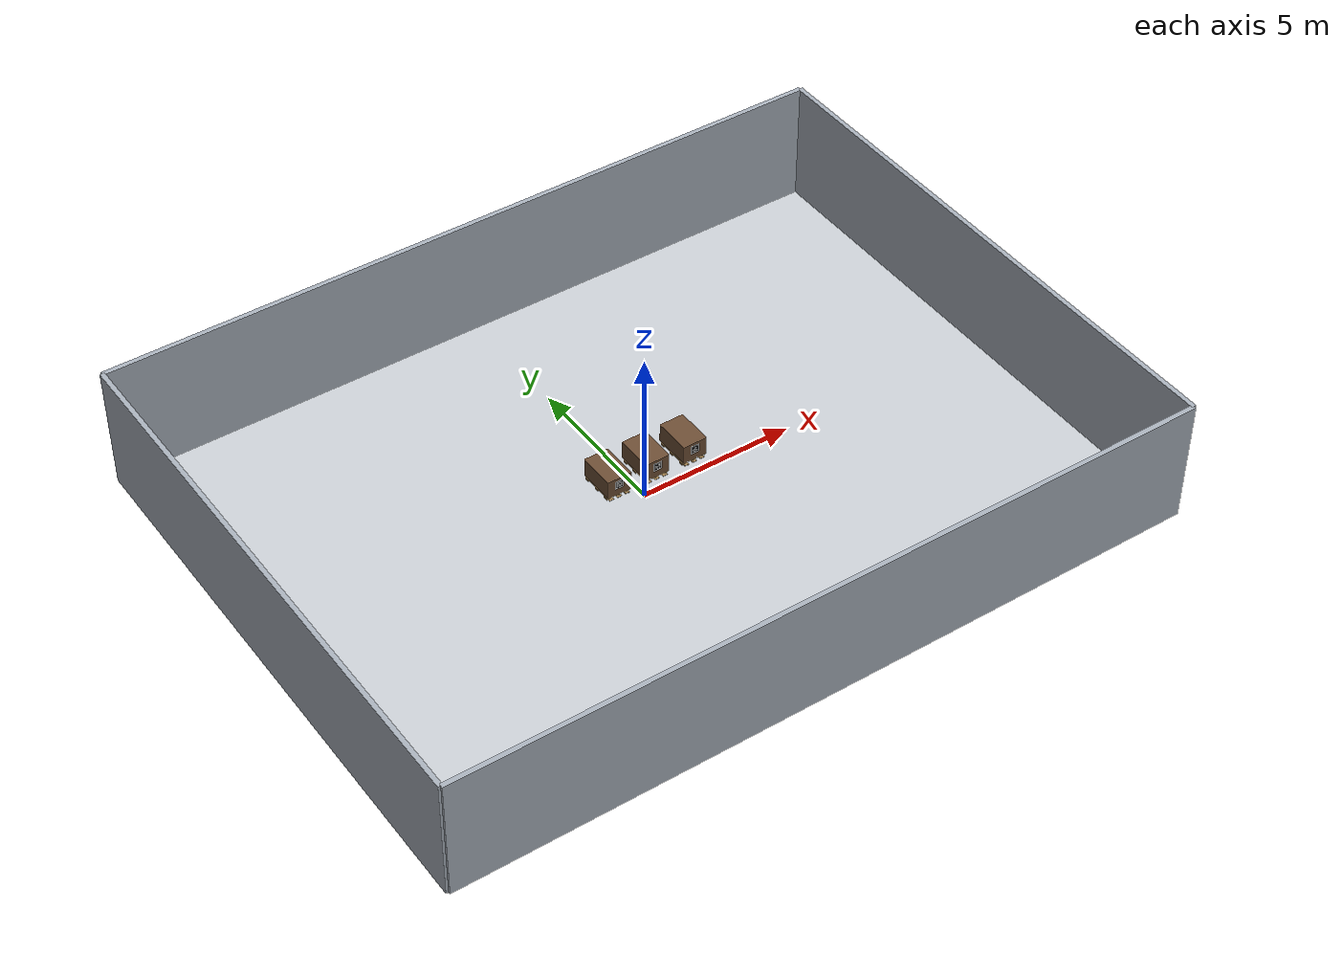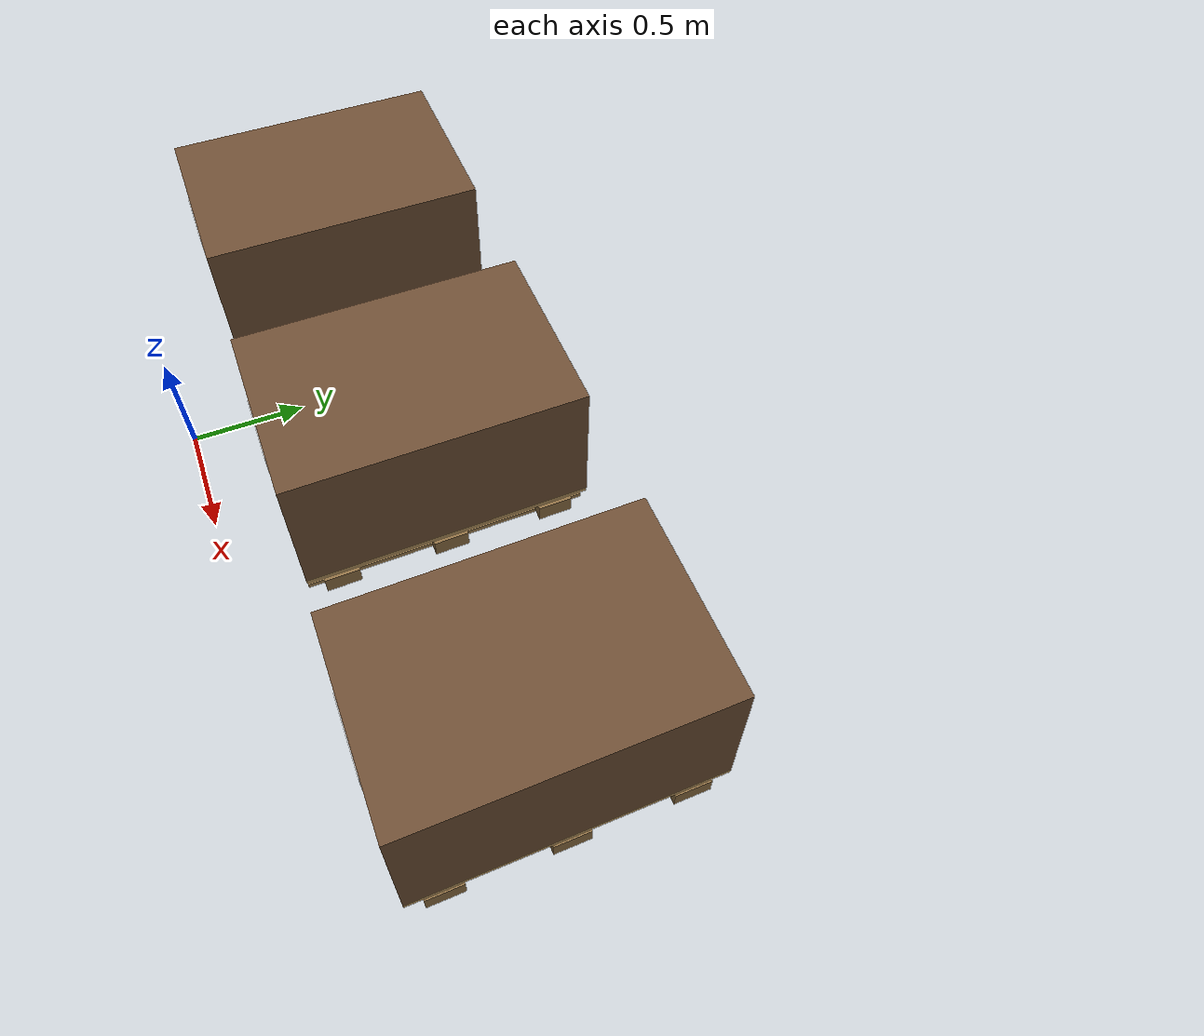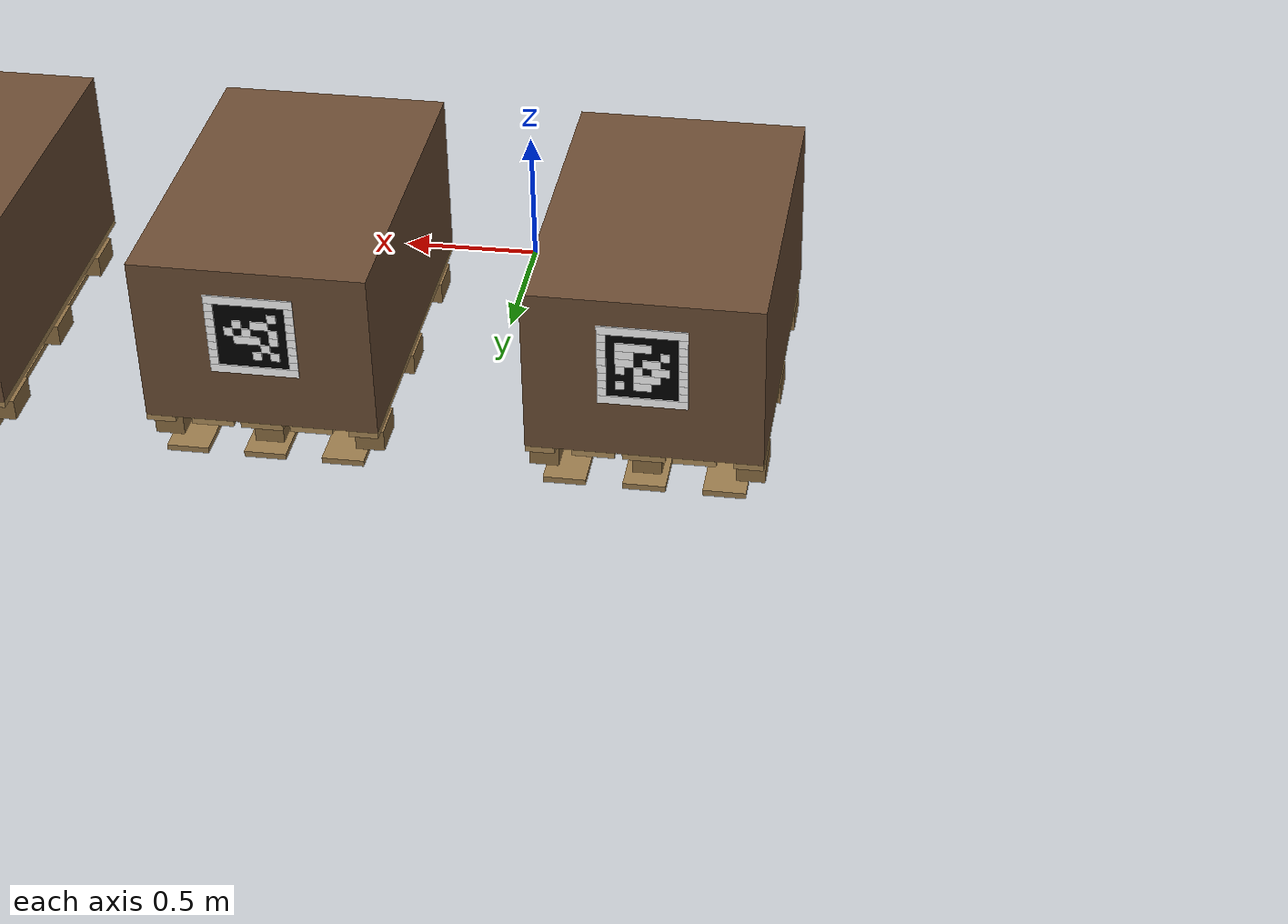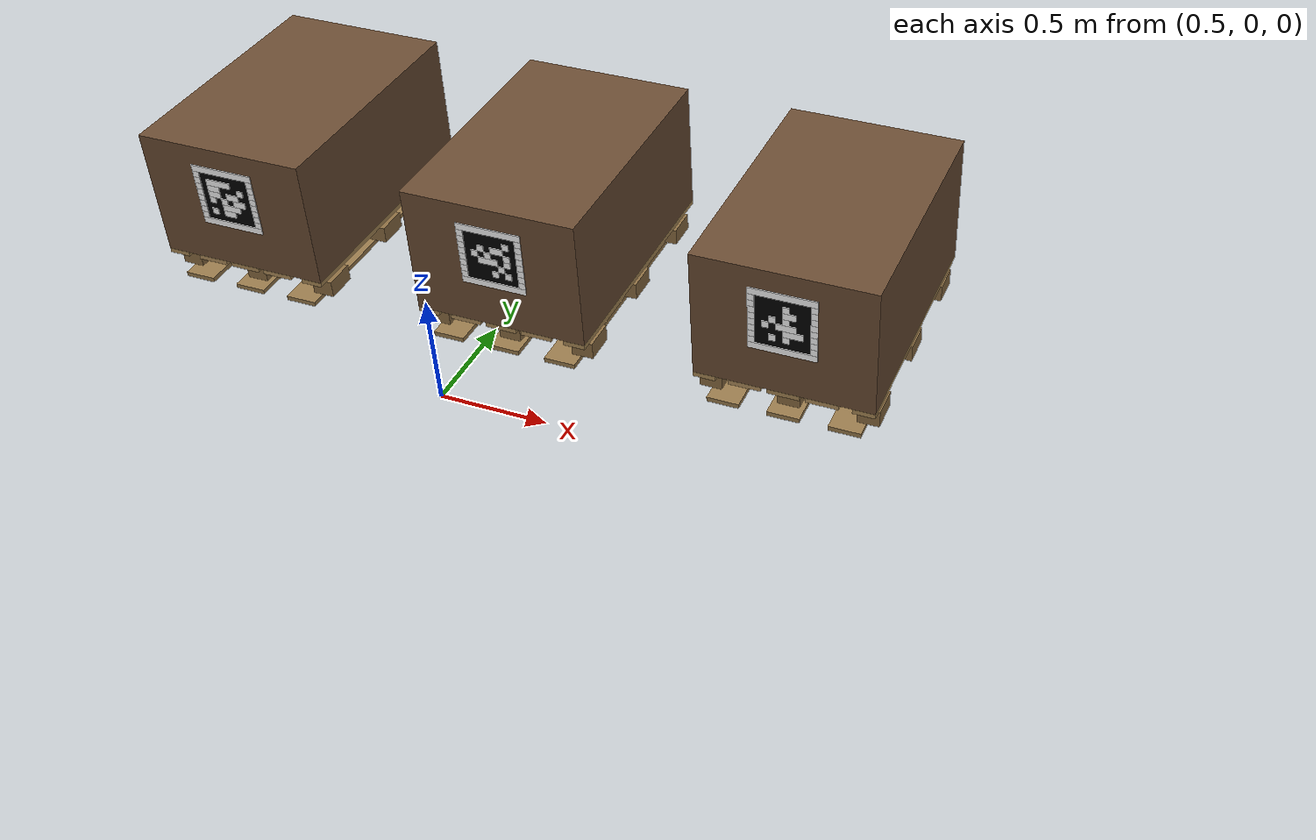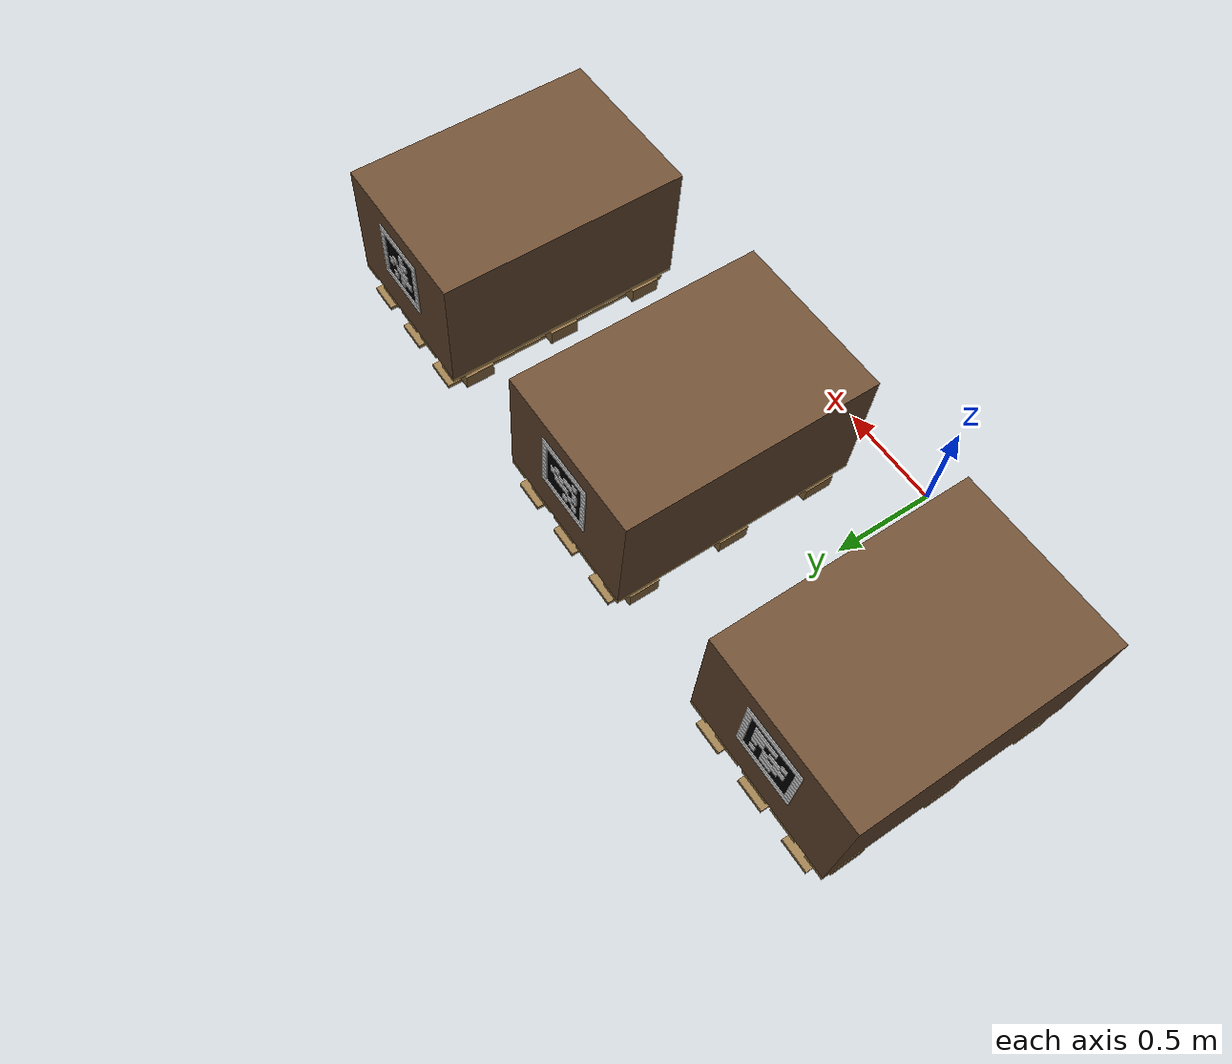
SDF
<sdf version="1.9">
 <world name="demo_room">
  <gravity>0 0 -9.81</gravity>
  <magnetic_field>6e-06 2.3e-05 -4.2e-05</magnetic_field>
  <physics name="dart_physics" type="dart">
   <max_step_size>0.001</max_step_size>
   <real_time_factor>1.0</real_time_factor>
   <real_time_update_rate>1000</real_time_update_rate>
  </physics>
  <plugin filename="gz-sim-physics-system" name="gz::sim::systems::Physics"/>
  <plugin filename="gz-sim-user-commands-system" name="gz::sim::systems::UserCommands"/>
  <plugin filename="gz-sim-scene-broadcaster-system" name="gz::sim::systems::SceneBroadcaster"/>
  <plugin filename="gz-sim-sensors-system" name="gz::sim::systems::Sensors">
   <render_engine>ogre2</render_engine>
  </plugin>
  <light type="directional" name="sun">
   <pose>0 0 10 0 0 0</pose>
   <diffuse>0.9 0.9 0.9 1.0</diffuse>
   <specular>0.2 0.2 0.2 1.0</specular>
   <attenuation>
    <range>1000</range>
    <constant>0.9</constant>
    <linear>0.01</linear>
    <quadratic>0.001</quadratic>
   </attenuation>
   <direction>-0.4 0.1 -0.9</direction>
  </light>
  <model name="floor">
   <static>true</static>
   <link name="floor_link">
    <collision name="floor_collision">
     <geometry><box><size>24 18 0.1</size></box></geometry>
     <surface>
      <friction>
       <ode><mu>200.0</mu><mu2>200.0</mu2><slip1>0.0</slip1><slip2>0.0</slip2></ode>
       <bullet><friction>200.0</friction><friction2>200.0</friction2></bullet>
      </friction>
     </surface>
    </collision>
    <visual name="floor_visual">
     <geometry><box><size>24 18 0.1</size></box></geometry>
     <material><ambient>0.78 0.80 0.82 1.0</ambient><diffuse>0.78 0.80 0.82 1.0</diffuse></material>
    </visual>
   </link>
  </model>
  <model name="north_wall">
   <static>true</static>
   <pose>0 9 2 0 0 0</pose>
   <link name="link">
    <collision name="collision"><geometry><box><size>24 0.15 4.0</size></box></geometry></collision>
    <visual name="visual">
     <geometry><box><size>24 0.15 4.0</size></box></geometry>
     <material><ambient>0.65 0.68 0.72 1.0</ambient><diffuse>0.65 0.68 0.72 1.0</diffuse></material>
    </visual>
   </link>
  </model>
  <model name="south_wall">
   <static>true</static>
   <pose>0 -9 2 0 0 0</pose>
   <link name="link">
    <collision name="collision"><geometry><box><size>24 0.15 4.0</size></box></geometry></collision>
    <visual name="visual">
     <geometry><box><size>24 0.15 4.0</size></box></geometry>
     <material><ambient>0.65 0.68 0.72 1.0</ambient><diffuse>0.65 0.68 0.72 1.0</diffuse></material>
    </visual>
   </link>
  </model>
  <model name="east_wall">
   <static>true</static>
   <pose>12 0 2 0 0 0</pose>
   <link name="link">
    <collision name="collision"><geometry><box><size>0.15 18 4.0</size></box></geometry></collision>
    <visual name="visual">
     <geometry><box><size>0.15 18 4.0</size></box></geometry>
     <material><ambient>0.65 0.68 0.72 1.0</ambient><diffuse>0.65 0.68 0.72 1.0</diffuse></material>
    </visual>
   </link>
  </model>
  <model name="west_wall">
   <static>true</static>
   <pose>-12 0 2 0 0 0</pose>
   <link name="link">
    <collision name="collision"><geometry><box><size>0.15 18 4.0</size></box></geometry></collision>
    <visual name="visual">
     <geometry><box><size>0.15 18 4.0</size></box></geometry>
     <material><ambient>0.65 0.68 0.72 1.0</ambient><diffuse>0.65 0.68 0.72 1.0</diffuse></material>
    </visual>
   </link>
  </model>
  <include>
   <name>pallet_b_south_05</name>
   <uri>model://euro_pallet_tag36h11_05</uri>
   <pose>-0.65 0.90 0 0 0 1.57079632679</pose>
   <static>false</static>
  </include>
  <include>
   <name>pallet_b_south_06</name>
   <uri>model://euro_pallet_tag36h11_06</uri>
   <pose>0.65 0.90 0 0 0 1.57079632679</pose>
   <static>false</static>
  </include>
  <include>
   <name>pallet_b_south_07</name>
   <uri>model://euro_pallet_tag36h11_07</uri>
   <pose>1.95 0.90 0 0 0 1.57079632679</pose>
   <static>false</static>
  </include>
 </world>
</sdf>

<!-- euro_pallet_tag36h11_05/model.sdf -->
<sdf version="1.9">
  <model name="euro_pallet_tag36h11_05">
    <pose>0 0 0 0 0 0</pose>
    <static>false</static>
    <self_collide>false</self_collide>
    <allow_auto_disable>false</allow_auto_disable>

    <link name="pallet_link">
      <pose>0 0 0.06 0 0 0</pose>
      <inertial>
        <pose>0 0 0.072 0 0 0</pose>
        <mass>25.0</mass>
        <inertia>
          <ixx>1.38</ixx>
          <iyy>3.04</iyy>
          <izz>4.33</izz>
          <ixy>0.0</ixy>
          <ixz>0.0</ixz>
          <iyz>0.0</iyz>
        </inertia>
      </inertial>

      <collision name="top_board_outer_left_collision">
        <pose>0 -0.35 0.133 0 0 0</pose>
        <geometry>
          <box>
            <size>1.2 0.10 0.022</size>
          </box>
        </geometry>
      </collision>
      <collision name="top_board_inner_left_collision">
        <pose>0 -0.17 0.133 0 0 0</pose>
        <geometry>
          <box>
            <size>1.2 0.145 0.022</size>
          </box>
        </geometry>
      </collision>
      <collision name="top_board_center_collision">
        <pose>0 0 0.133 0 0 0</pose>
        <geometry>
          <box>
            <size>1.2 0.145 0.022</size>
          </box>
        </geometry>
      </collision>
      <collision name="top_board_inner_right_collision">
        <pose>0 0.17 0.133 0 0 0</pose>
        <geometry>
          <box>
            <size>1.2 0.145 0.022</size>
          </box>
        </geometry>
      </collision>
      <collision name="top_board_outer_right_collision">
        <pose>0 0.35 0.133 0 0 0</pose>
        <geometry>
          <box>
            <size>1.2 0.10 0.022</size>
          </box>
        </geometry>
      </collision>

      <collision name="bottom_board_left_collision">
        <pose>0 -0.34 0.011 0 0 0</pose>
        <geometry>
          <box>
            <size>1.2 0.10 0.022</size>
          </box>
        </geometry>
        <surface>
          <friction>
            <ode>
              <mu>1.2</mu>
              <mu2>1.2</mu2>
              <slip1>0.0</slip1>
              <slip2>0.0</slip2>
            </ode>
            <bullet>
              <friction>1.2</friction>
              <friction2>1.2</friction2>
            </bullet>
          </friction>
        </surface>
      </collision>
      <collision name="bottom_board_center_collision">
        <pose>0 0 0.011 0 0 0</pose>
        <geometry>
          <box>
            <size>1.2 0.10 0.022</size>
          </box>
        </geometry>
        <surface>
          <friction>
            <ode>
              <mu>1.2</mu>
              <mu2>1.2</mu2>
              <slip1>0.0</slip1>
              <slip2>0.0</slip2>
            </ode>
            <bullet>
              <friction>1.2</friction>
              <friction2>1.2</friction2>
            </bullet>
          </friction>
        </surface>
      </collision>
      <collision name="bottom_board_right_collision">
        <pose>0 0.34 0.011 0 0 0</pose>
        <geometry>
          <box>
            <size>1.2 0.10 0.022</size>
          </box>
        </geometry>
        <surface>
          <friction>
            <ode>
              <mu>1.2</mu>
              <mu2>1.2</mu2>
              <slip1>0.0</slip1>
              <slip2>0.0</slip2>
            </ode>
            <bullet>
              <friction>1.2</friction>
              <friction2>1.2</friction2>
            </bullet>
          </friction>
        </surface>
      </collision>

      <collision name="block_1_collision">
        <pose>-0.46 -0.35 0.061 0 0 0</pose>
        <geometry>
          <box>
            <size>0.145 0.10 0.078</size>
          </box>
        </geometry>
      </collision>
      <collision name="block_2_collision">
        <pose>0 -0.35 0.061 0 0 0</pose>
        <geometry>
          <box>
            <size>0.145 0.10 0.078</size>
          </box>
        </geometry>
      </collision>
      <collision name="block_3_collision">
        <pose>0.46 -0.35 0.061 0 0 0</pose>
        <geometry>
          <box>
            <size>0.145 0.10 0.078</size>
          </box>
        </geometry>
      </collision>
      <collision name="block_4_collision">
        <pose>-0.46 0 0.061 0 0 0</pose>
        <geometry>
          <box>
            <size>0.145 0.10 0.078</size>
          </box>
        </geometry>
      </collision>
      <collision name="block_5_collision">
        <pose>0 0 0.061 0 0 0</pose>
        <geometry>
          <box>
            <size>0.145 0.10 0.078</size>
          </box>
        </geometry>
      </collision>
      <collision name="block_6_collision">
        <pose>0.46 0 0.061 0 0 0</pose>
        <geometry>
          <box>
            <size>0.145 0.10 0.078</size>
          </box>
        </geometry>
      </collision>
      <collision name="block_7_collision">
        <pose>-0.46 0.35 0.061 0 0 0</pose>
        <geometry>
          <box>
            <size>0.145 0.10 0.078</size>
          </box>
        </geometry>
      </collision>
      <collision name="block_8_collision">
        <pose>0 0.35 0.061 0 0 0</pose>
        <geometry>
          <box>
            <size>0.145 0.10 0.078</size>
          </box>
        </geometry>
      </collision>
      <collision name="block_9_collision">
        <pose>0.46 0.35 0.061 0 0 0</pose>
        <geometry>
          <box>
            <size>0.145 0.10 0.078</size>
          </box>
        </geometry>
      </collision>
      <collision name="marker_box_collision">
        <pose>0 0 0.444 0 0 0</pose>
        <geometry>
          <box>
            <size>1.2 0.8 0.60</size>
          </box>
        </geometry>
      </collision>

      <visual name="top_board_outer_left">
        <pose>0 -0.35 0.133 0 0 0</pose>
        <geometry>
          <box>
            <size>1.2 0.10 0.022</size>
          </box>
        </geometry>
        <material>
          <ambient>0.67 0.54 0.34 1.0</ambient>
          <diffuse>0.67 0.54 0.34 1.0</diffuse>
        </material>
      </visual>
      <visual name="top_board_inner_left">
        <pose>0 -0.17 0.133 0 0 0</pose>
        <geometry>
          <box>
            <size>1.2 0.145 0.022</size>
          </box>
        </geometry>
        <material>
          <ambient>0.69 0.56 0.36 1.0</ambient>
          <diffuse>0.69 0.56 0.36 1.0</diffuse>
        </material>
      </visual>
      <visual name="top_board_center">
        <pose>0 0 0.133 0 0 0</pose>
        <geometry>
          <box>
            <size>1.2 0.145 0.022</size>
          </box>
        </geometry>
        <material>
          <ambient>0.66 0.53 0.33 1.0</ambient>
          <diffuse>0.66 0.53 0.33 1.0</diffuse>
        </material>
      </visual>
      <visual name="top_board_inner_right">
        <pose>0 0.17 0.133 0 0 0</pose>
        <geometry>
          <box>
            <size>1.2 0.145 0.022</size>
          </box>
        </geometry>
        <material>
          <ambient>0.69 0.56 0.36 1.0</ambient>
          <diffuse>0.69 0.56 0.36 1.0</diffuse>
        </material>
      </visual>
      <visual name="top_board_outer_right">
        <pose>0 0.35 0.133 0 0 0</pose>
        <geometry>
          <box>
            <size>1.2 0.10 0.022</size>
          </box>
        </geometry>
        <material>
          <ambient>0.67 0.54 0.34 1.0</ambient>
          <diffuse>0.67 0.54 0.34 1.0</diffuse>
        </material>
      </visual>

      <visual name="bottom_board_left">
        <pose>0 -0.27 0.011 0 0 0</pose>
        <geometry>
          <box>
            <size>1.2 0.145 0.022</size>
          </box>
        </geometry>
        <material>
          <ambient>0.60 0.48 0.30 1.0</ambient>
          <diffuse>0.60 0.48 0.30 1.0</diffuse>
        </material>
      </visual>
      <visual name="bottom_board_center">
        <pose>0 0 0.011 0 0 0</pose>
        <geometry>
          <box>
            <size>1.2 0.145 0.022</size>
          </box>
        </geometry>
        <material>
          <ambient>0.60 0.48 0.30 1.0</ambient>
          <diffuse>0.60 0.48 0.30 1.0</diffuse>
        </material>
      </visual>
      <visual name="bottom_board_right">
        <pose>0 0.27 0.011 0 0 0</pose>
        <geometry>
          <box>
            <size>1.2 0.145 0.022</size>
          </box>
        </geometry>
        <material>
          <ambient>0.60 0.48 0.30 1.0</ambient>
          <diffuse>0.60 0.48 0.30 1.0</diffuse>
        </material>
      </visual>

      <visual name="block_1">
        <pose>-0.46 -0.35 0.061 0 0 0</pose>
        <geometry>
          <box>
            <size>0.145 0.10 0.078</size>
          </box>
        </geometry>
        <material>
          <ambient>0.55 0.43 0.26 1.0</ambient>
          <diffuse>0.55 0.43 0.26 1.0</diffuse>
        </material>
      </visual>
      <visual name="block_2">
        <pose>0 -0.35 0.061 0 0 0</pose>
        <geometry>
          <box>
            <size>0.145 0.10 0.078</size>
          </box>
        </geometry>
        <material>
          <ambient>0.55 0.43 0.26 1.0</ambient>
          <diffuse>0.55 0.43 0.26 1.0</diffuse>
        </material>
      </visual>
      <visual name="block_3">
        <pose>0.46 -0.35 0.061 0 0 0</pose>
        <geometry>
          <box>
            <size>0.145 0.10 0.078</size>
          </box>
        </geometry>
        <material>
          <ambient>0.55 0.43 0.26 1.0</ambient>
          <diffuse>0.55 0.43 0.26 1.0</diffuse>
        </material>
      </visual>
      <visual name="block_4">
        <pose>-0.46 0 0.061 0 0 0</pose>
        <geometry>
          <box>
            <size>0.145 0.10 0.078</size>
          </box>
        </geometry>
        <material>
          <ambient>0.55 0.43 0.26 1.0</ambient>
          <diffuse>0.55 0.43 0.26 1.0</diffuse>
        </material>
      </visual>
      <visual name="block_5">
        <pose>0 0 0.061 0 0 0</pose>
        <geometry>
          <box>
            <size>0.145 0.10 0.078</size>
          </box>
        </geometry>
        <material>
          <ambient>0.55 0.43 0.26 1.0</ambient>
          <diffuse>0.55 0.43 0.26 1.0</diffuse>
        </material>
      </visual>
      <visual name="block_6">
        <pose>0.46 0 0.061 0 0 0</pose>
        <geometry>
          <box>
            <size>0.145 0.10 0.078</size>
          </box>
        </geometry>
        <material>
          <ambient>0.55 0.43 0.26 1.0</ambient>
          <diffuse>0.55 0.43 0.26 1.0</diffuse>
        </material>
      </visual>
      <visual name="block_7">
        <pose>-0.46 0.35 0.061 0 0 0</pose>
        <geometry>
          <box>
            <size>0.145 0.10 0.078</size>
          </box>
        </geometry>
        <material>
          <ambient>0.55 0.43 0.26 1.0</ambient>
          <diffuse>0.55 0.43 0.26 1.0</diffuse>
        </material>
      </visual>
      <visual name="block_8">
        <pose>0 0.35 0.061 0 0 0</pose>
        <geometry>
          <box>
            <size>0.145 0.10 0.078</size>
          </box>
        </geometry>
        <material>
          <ambient>0.55 0.43 0.26 1.0</ambient>
          <diffuse>0.55 0.43 0.26 1.0</diffuse>
        </material>
      </visual>
      <visual name="block_9">
        <pose>0.46 0.35 0.061 0 0 0</pose>
        <geometry>
          <box>
            <size>0.145 0.10 0.078</size>
          </box>
        </geometry>
        <material>
          <ambient>0.55 0.43 0.26 1.0</ambient>
          <diffuse>0.55 0.43 0.26 1.0</diffuse>
        </material>
      </visual>
      <visual name="apriltag_front_black_plate">
        <pose>0.602 0 0.500 0 0 0</pose>
        <geometry>
          <box>
            <size>0.002 0.300 0.300</size>
          </box>
        </geometry>
        <material>
          <ambient>0 0 0 1</ambient>
          <diffuse>0 0 0 1</diffuse>
          <specular>0 0 0 1</specular>
        </material>
      </visual>
      <visual name="apriltag_front_white_r00_00_09">
        <pose>0.605 0.000 0.635 0 0 0</pose>
        <geometry>
          <box>
            <size>0.003 0.300 0.030</size>
          </box>
        </geometry>
        <material>
          <ambient>1 1 1 1</ambient>
          <diffuse>1 1 1 1</diffuse>
          <specular>0.05 0.05 0.05 1</specular>
        </material>
      </visual>
      <visual name="apriltag_front_white_r01_00_00">
        <pose>0.605 -0.135 0.605 0 0 0</pose>
        <geometry>
          <box>
            <size>0.003 0.030 0.030</size>
          </box>
        </geometry>
        <material>
          <ambient>1 1 1 1</ambient>
          <diffuse>1 1 1 1</diffuse>
          <specular>0.05 0.05 0.05 1</specular>
        </material>
      </visual>
      <visual name="apriltag_front_white_r01_09_09">
        <pose>0.605 0.135 0.605 0 0 0</pose>
        <geometry>
          <box>
            <size>0.003 0.030 0.030</size>
          </box>
        </geometry>
        <material>
          <ambient>1 1 1 1</ambient>
          <diffuse>1 1 1 1</diffuse>
          <specular>0.05 0.05 0.05 1</specular>
        </material>
      </visual>
      <visual name="apriltag_front_white_r02_00_00">
        <pose>0.605 -0.135 0.575 0 0 0</pose>
        <geometry>
          <box>
            <size>0.003 0.030 0.030</size>
          </box>
        </geometry>
        <material>
          <ambient>1 1 1 1</ambient>
          <diffuse>1 1 1 1</diffuse>
          <specular>0.05 0.05 0.05 1</specular>
        </material>
      </visual>
      <visual name="apriltag_front_white_r02_02_05">
        <pose>0.605 -0.030 0.575 0 0 0</pose>
        <geometry>
          <box>
            <size>0.003 0.120 0.030</size>
          </box>
        </geometry>
        <material>
          <ambient>1 1 1 1</ambient>
          <diffuse>1 1 1 1</diffuse>
          <specular>0.05 0.05 0.05 1</specular>
        </material>
      </visual>
      <visual name="apriltag_front_white_r02_09_09">
        <pose>0.605 0.135 0.575 0 0 0</pose>
        <geometry>
          <box>
            <size>0.003 0.030 0.030</size>
          </box>
        </geometry>
        <material>
          <ambient>1 1 1 1</ambient>
          <diffuse>1 1 1 1</diffuse>
          <specular>0.05 0.05 0.05 1</specular>
        </material>
      </visual>
      <visual name="apriltag_front_white_r03_00_00">
        <pose>0.605 -0.135 0.545 0 0 0</pose>
        <geometry>
          <box>
            <size>0.003 0.030 0.030</size>
          </box>
        </geometry>
        <material>
          <ambient>1 1 1 1</ambient>
          <diffuse>1 1 1 1</diffuse>
          <specular>0.05 0.05 0.05 1</specular>
        </material>
      </visual>
      <visual name="apriltag_front_white_r03_02_03">
        <pose>0.605 -0.060 0.545 0 0 0</pose>
        <geometry>
          <box>
            <size>0.003 0.060 0.030</size>
          </box>
        </geometry>
        <material>
          <ambient>1 1 1 1</ambient>
          <diffuse>1 1 1 1</diffuse>
          <specular>0.05 0.05 0.05 1</specular>
        </material>
      </visual>
      <visual name="apriltag_front_white_r03_07_07">
        <pose>0.605 0.075 0.545 0 0 0</pose>
        <geometry>
          <box>
            <size>0.003 0.030 0.030</size>
          </box>
        </geometry>
        <material>
          <ambient>1 1 1 1</ambient>
          <diffuse>1 1 1 1</diffuse>
          <specular>0.05 0.05 0.05 1</specular>
        </material>
      </visual>
      <visual name="apriltag_front_white_r03_09_09">
        <pose>0.605 0.135 0.545 0 0 0</pose>
        <geometry>
          <box>
            <size>0.003 0.030 0.030</size>
          </box>
        </geometry>
        <material>
          <ambient>1 1 1 1</ambient>
          <diffuse>1 1 1 1</diffuse>
          <specular>0.05 0.05 0.05 1</specular>
        </material>
      </visual>
      <visual name="apriltag_front_white_r04_00_00">
        <pose>0.605 -0.135 0.515 0 0 0</pose>
        <geometry>
          <box>
            <size>0.003 0.030 0.030</size>
          </box>
        </geometry>
        <material>
          <ambient>1 1 1 1</ambient>
          <diffuse>1 1 1 1</diffuse>
          <specular>0.05 0.05 0.05 1</specular>
        </material>
      </visual>
      <visual name="apriltag_front_white_r04_02_03">
        <pose>0.605 -0.060 0.515 0 0 0</pose>
        <geometry>
          <box>
            <size>0.003 0.060 0.030</size>
          </box>
        </geometry>
        <material>
          <ambient>1 1 1 1</ambient>
          <diffuse>1 1 1 1</diffuse>
          <specular>0.05 0.05 0.05 1</specular>
        </material>
      </visual>
      <visual name="apriltag_front_white_r04_05_06">
        <pose>0.605 0.030 0.515 0 0 0</pose>
        <geometry>
          <box>
            <size>0.003 0.060 0.030</size>
          </box>
        </geometry>
        <material>
          <ambient>1 1 1 1</ambient>
          <diffuse>1 1 1 1</diffuse>
          <specular>0.05 0.05 0.05 1</specular>
        </material>
      </visual>
      <visual name="apriltag_front_white_r04_09_09">
        <pose>0.605 0.135 0.515 0 0 0</pose>
        <geometry>
          <box>
            <size>0.003 0.030 0.030</size>
          </box>
        </geometry>
        <material>
          <ambient>1 1 1 1</ambient>
          <diffuse>1 1 1 1</diffuse>
          <specular>0.05 0.05 0.05 1</specular>
        </material>
      </visual>
      <visual name="apriltag_front_white_r05_00_00">
        <pose>0.605 -0.135 0.485 0 0 0</pose>
        <geometry>
          <box>
            <size>0.003 0.030 0.030</size>
          </box>
        </geometry>
        <material>
          <ambient>1 1 1 1</ambient>
          <diffuse>1 1 1 1</diffuse>
          <specular>0.05 0.05 0.05 1</specular>
        </material>
      </visual>
      <visual name="apriltag_front_white_r05_02_02">
        <pose>0.605 -0.075 0.485 0 0 0</pose>
        <geometry>
          <box>
            <size>0.003 0.030 0.030</size>
          </box>
        </geometry>
        <material>
          <ambient>1 1 1 1</ambient>
          <diffuse>1 1 1 1</diffuse>
          <specular>0.05 0.05 0.05 1</specular>
        </material>
      </visual>
      <visual name="apriltag_front_white_r05_04_04">
        <pose>0.605 -0.015 0.485 0 0 0</pose>
        <geometry>
          <box>
            <size>0.003 0.030 0.030</size>
          </box>
        </geometry>
        <material>
          <ambient>1 1 1 1</ambient>
          <diffuse>1 1 1 1</diffuse>
          <specular>0.05 0.05 0.05 1</specular>
        </material>
      </visual>
      <visual name="apriltag_front_white_r05_06_07">
        <pose>0.605 0.060 0.485 0 0 0</pose>
        <geometry>
          <box>
            <size>0.003 0.060 0.030</size>
          </box>
        </geometry>
        <material>
          <ambient>1 1 1 1</ambient>
          <diffuse>1 1 1 1</diffuse>
          <specular>0.05 0.05 0.05 1</specular>
        </material>
      </visual>
      <visual name="apriltag_front_white_r05_09_09">
        <pose>0.605 0.135 0.485 0 0 0</pose>
        <geometry>
          <box>
            <size>0.003 0.030 0.030</size>
          </box>
        </geometry>
        <material>
          <ambient>1 1 1 1</ambient>
          <diffuse>1 1 1 1</diffuse>
          <specular>0.05 0.05 0.05 1</specular>
        </material>
      </visual>
      <visual name="apriltag_front_white_r06_00_00">
        <pose>0.605 -0.135 0.455 0 0 0</pose>
        <geometry>
          <box>
            <size>0.003 0.030 0.030</size>
          </box>
        </geometry>
        <material>
          <ambient>1 1 1 1</ambient>
          <diffuse>1 1 1 1</diffuse>
          <specular>0.05 0.05 0.05 1</specular>
        </material>
      </visual>
      <visual name="apriltag_front_white_r06_04_06">
        <pose>0.605 0.015 0.455 0 0 0</pose>
        <geometry>
          <box>
            <size>0.003 0.090 0.030</size>
          </box>
        </geometry>
        <material>
          <ambient>1 1 1 1</ambient>
          <diffuse>1 1 1 1</diffuse>
          <specular>0.05 0.05 0.05 1</specular>
        </material>
      </visual>
      <visual name="apriltag_front_white_r06_09_09">
        <pose>0.605 0.135 0.455 0 0 0</pose>
        <geometry>
          <box>
            <size>0.003 0.030 0.030</size>
          </box>
        </geometry>
        <material>
          <ambient>1 1 1 1</ambient>
          <diffuse>1 1 1 1</diffuse>
          <specular>0.05 0.05 0.05 1</specular>
        </material>
      </visual>
      <visual name="apriltag_front_white_r07_00_00">
        <pose>0.605 -0.135 0.425 0 0 0</pose>
        <geometry>
          <box>
            <size>0.003 0.030 0.030</size>
          </box>
        </geometry>
        <material>
          <ambient>1 1 1 1</ambient>
          <diffuse>1 1 1 1</diffuse>
          <specular>0.05 0.05 0.05 1</specular>
        </material>
      </visual>
      <visual name="apriltag_front_white_r07_02_02">
        <pose>0.605 -0.075 0.425 0 0 0</pose>
        <geometry>
          <box>
            <size>0.003 0.030 0.030</size>
          </box>
        </geometry>
        <material>
          <ambient>1 1 1 1</ambient>
          <diffuse>1 1 1 1</diffuse>
          <specular>0.05 0.05 0.05 1</specular>
        </material>
      </visual>
      <visual name="apriltag_front_white_r07_04_05">
        <pose>0.605 0.000 0.425 0 0 0</pose>
        <geometry>
          <box>
            <size>0.003 0.060 0.030</size>
          </box>
        </geometry>
        <material>
          <ambient>1 1 1 1</ambient>
          <diffuse>1 1 1 1</diffuse>
          <specular>0.05 0.05 0.05 1</specular>
        </material>
      </visual>
      <visual name="apriltag_front_white_r07_09_09">
        <pose>0.605 0.135 0.425 0 0 0</pose>
        <geometry>
          <box>
            <size>0.003 0.030 0.030</size>
          </box>
        </geometry>
        <material>
          <ambient>1 1 1 1</ambient>
          <diffuse>1 1 1 1</diffuse>
          <specular>0.05 0.05 0.05 1</specular>
        </material>
      </visual>
      <visual name="apriltag_front_white_r08_00_00">
        <pose>0.605 -0.135 0.395 0 0 0</pose>
        <geometry>
          <box>
            <size>0.003 0.030 0.030</size>
          </box>
        </geometry>
        <material>
          <ambient>1 1 1 1</ambient>
          <diffuse>1 1 1 1</diffuse>
          <specular>0.05 0.05 0.05 1</specular>
        </material>
      </visual>
      <visual name="apriltag_front_white_r08_09_09">
        <pose>0.605 0.135 0.395 0 0 0</pose>
        <geometry>
          <box>
            <size>0.003 0.030 0.030</size>
          </box>
        </geometry>
        <material>
          <ambient>1 1 1 1</ambient>
          <diffuse>1 1 1 1</diffuse>
          <specular>0.05 0.05 0.05 1</specular>
        </material>
      </visual>
      <visual name="apriltag_front_white_r09_00_09">
        <pose>0.605 0.000 0.365 0 0 0</pose>
        <geometry>
          <box>
            <size>0.003 0.300 0.030</size>
          </box>
        </geometry>
        <material>
          <ambient>1 1 1 1</ambient>
          <diffuse>1 1 1 1</diffuse>
          <specular>0.05 0.05 0.05 1</specular>
        </material>
      </visual>
      <visual name="apriltag_back_black_plate">
        <pose>-0.602 0 0.500 0 0 0</pose>
        <geometry>
          <box>
            <size>0.002 0.300 0.300</size>
          </box>
        </geometry>
        <material>
          <ambient>0 0 0 1</ambient>
          <diffuse>0 0 0 1</diffuse>
          <specular>0 0 0 1</specular>
        </material>
      </visual>
      <visual name="apriltag_back_white_r00_00_09">
        <pose>-0.605 -0.000 0.635 0 0 0</pose>
        <geometry>
          <box>
            <size>0.003 0.300 0.030</size>
          </box>
        </geometry>
        <material>
          <ambient>1 1 1 1</ambient>
          <diffuse>1 1 1 1</diffuse>
          <specular>0.05 0.05 0.05 1</specular>
        </material>
      </visual>
      <visual name="apriltag_back_white_r01_00_00">
        <pose>-0.605 0.135 0.605 0 0 0</pose>
        <geometry>
          <box>
            <size>0.003 0.030 0.030</size>
          </box>
        </geometry>
        <material>
          <ambient>1 1 1 1</ambient>
          <diffuse>1 1 1 1</diffuse>
          <specular>0.05 0.05 0.05 1</specular>
        </material>
      </visual>
      <visual name="apriltag_back_white_r01_09_09">
        <pose>-0.605 -0.135 0.605 0 0 0</pose>
        <geometry>
          <box>
            <size>0.003 0.030 0.030</size>
          </box>
        </geometry>
        <material>
          <ambient>1 1 1 1</ambient>
          <diffuse>1 1 1 1</diffuse>
          <specular>0.05 0.05 0.05 1</specular>
        </material>
      </visual>
      <visual name="apriltag_back_white_r02_00_00">
        <pose>-0.605 0.135 0.575 0 0 0</pose>
        <geometry>
          <box>
            <size>0.003 0.030 0.030</size>
          </box>
        </geometry>
        <material>
          <ambient>1 1 1 1</ambient>
          <diffuse>1 1 1 1</diffuse>
          <specular>0.05 0.05 0.05 1</specular>
        </material>
      </visual>
      <visual name="apriltag_back_white_r02_02_05">
        <pose>-0.605 0.030 0.575 0 0 0</pose>
        <geometry>
          <box>
            <size>0.003 0.120 0.030</size>
          </box>
        </geometry>
        <material>
          <ambient>1 1 1 1</ambient>
          <diffuse>1 1 1 1</diffuse>
          <specular>0.05 0.05 0.05 1</specular>
        </material>
      </visual>
      <visual name="apriltag_back_white_r02_09_09">
        <pose>-0.605 -0.135 0.575 0 0 0</pose>
        <geometry>
          <box>
            <size>0.003 0.030 0.030</size>
          </box>
        </geometry>
        <material>
          <ambient>1 1 1 1</ambient>
          <diffuse>1 1 1 1</diffuse>
          <specular>0.05 0.05 0.05 1</specular>
        </material>
      </visual>
      <visual name="apriltag_back_white_r03_00_00">
        <pose>-0.605 0.135 0.545 0 0 0</pose>
        <geometry>
          <box>
            <size>0.003 0.030 0.030</size>
          </box>
        </geometry>
        <material>
          <ambient>1 1 1 1</ambient>
          <diffuse>1 1 1 1</diffuse>
          <specular>0.05 0.05 0.05 1</specular>
        </material>
      </visual>
      <visual name="apriltag_back_white_r03_02_03">
        <pose>-0.605 0.060 0.545 0 0 0</pose>
        <geometry>
          <box>
            <size>0.003 0.060 0.030</size>
          </box>
        </geometry>
        <material>
          <ambient>1 1 1 1</ambient>
          <diffuse>1 1 1 1</diffuse>
          <specular>0.05 0.05 0.05 1</specular>
        </material>
      </visual>
      <visual name="apriltag_back_white_r03_07_07">
        <pose>-0.605 -0.075 0.545 0 0 0</pose>
        <geometry>
          <box>
            <size>0.003 0.030 0.030</size>
          </box>
        </geometry>
        <material>
          <ambient>1 1 1 1</ambient>
          <diffuse>1 1 1 1</diffuse>
          <specular>0.05 0.05 0.05 1</specular>
        </material>
      </visual>
      <visual name="apriltag_back_white_r03_09_09">
        <pose>-0.605 -0.135 0.545 0 0 0</pose>
        <geometry>
          <box>
            <size>0.003 0.030 0.030</size>
          </box>
        </geometry>
        <material>
          <ambient>1 1 1 1</ambient>
          <diffuse>1 1 1 1</diffuse>
          <specular>0.05 0.05 0.05 1</specular>
        </material>
      </visual>
      <visual name="apriltag_back_white_r04_00_00">
        <pose>-0.605 0.135 0.515 0 0 0</pose>
        <geometry>
          <box>
            <size>0.003 0.030 0.030</size>
          </box>
        </geometry>
        <material>
          <ambient>1 1 1 1</ambient>
          <diffuse>1 1 1 1</diffuse>
          <specular>0.05 0.05 0.05 1</specular>
        </material>
      </visual>
      <visual name="apriltag_back_white_r04_02_03">
        <pose>-0.605 0.060 0.515 0 0 0</pose>
        <geometry>
          <box>
            <size>0.003 0.060 0.030</size>
          </box>
        </geometry>
        <material>
          <ambient>1 1 1 1</ambient>
          <diffuse>1 1 1 1</diffuse>
          <specular>0.05 0.05 0.05 1</specular>
        </material>
      </visual>
      <visual name="apriltag_back_white_r04_05_06">
        <pose>-0.605 -0.030 0.515 0 0 0</pose>
        <geometry>
          <box>
            <size>0.003 0.060 0.030</size>
          </box>
        </geometry>
        <material>
          <ambient>1 1 1 1</ambient>
          <diffuse>1 1 1 1</diffuse>
          <specular>0.05 0.05 0.05 1</specular>
        </material>
      </visual>
      <visual name="apriltag_back_white_r04_09_09">
        <pose>-0.605 -0.135 0.515 0 0 0</pose>
        <geometry>
          <box>
            <size>0.003 0.030 0.030</size>
          </box>
        </geometry>
        <material>
          <ambient>1 1 1 1</ambient>
          <diffuse>1 1 1 1</diffuse>
          <specular>0.05 0.05 0.05 1</specular>
        </material>
      </visual>
      <visual name="apriltag_back_white_r05_00_00">
        <pose>-0.605 0.135 0.485 0 0 0</pose>
        <geometry>
          <box>
            <size>0.003 0.030 0.030</size>
          </box>
        </geometry>
        <material>
          <ambient>1 1 1 1</ambient>
          <diffuse>1 1 1 1</diffuse>
          <specular>0.05 0.05 0.05 1</specular>
        </material>
      </visual>
      <visual name="apriltag_back_white_r05_02_02">
        <pose>-0.605 0.075 0.485 0 0 0</pose>
        <geometry>
          <box>
            <size>0.003 0.030 0.030</size>
          </box>
        </geometry>
        <material>
          <ambient>1 1 1 1</ambient>
          <diffuse>1 1 1 1</diffuse>
          <specular>0.05 0.05 0.05 1</specular>
        </material>
      </visual>
      <visual name="apriltag_back_white_r05_04_04">
        <pose>-0.605 0.015 0.485 0 0 0</pose>
        <geometry>
          <box>
            <size>0.003 0.030 0.030</size>
          </box>
        </geometry>
        <material>
          <ambient>1 1 1 1</ambient>
          <diffuse>1 1 1 1</diffuse>
          <specular>0.05 0.05 0.05 1</specular>
        </material>
      </visual>
      <visual name="apriltag_back_white_r05_06_07">
        <pose>-0.605 -0.060 0.485 0 0 0</pose>
        <geometry>
          <box>
            <size>0.003 0.060 0.030</size>
          </box>
        </geometry>
        <material>
          <ambient>1 1 1 1</ambient>
          <diffuse>1 1 1 1</diffuse>
          <specular>0.05 0.05 0.05 1</specular>
        </material>
      </visual>
      <visual name="apriltag_back_white_r05_09_09">
        <pose>-0.605 -0.135 0.485 0 0 0</pose>
        <geometry>
          <box>
            <size>0.003 0.030 0.030</size>
          </box>
        </geometry>
        <material>
          <ambient>1 1 1 1</ambient>
          <diffuse>1 1 1 1</diffuse>
          <specular>0.05 0.05 0.05 1</specular>
        </material>
      </visual>
      <visual name="apriltag_back_white_r06_00_00">
        <pose>-0.605 0.135 0.455 0 0 0</pose>
        <geometry>
          <box>
            <size>0.003 0.030 0.030</size>
          </box>
        </geometry>
        <material>
          <ambient>1 1 1 1</ambient>
          <diffuse>1 1 1 1</diffuse>
          <specular>0.05 0.05 0.05 1</specular>
        </material>
      </visual>
      <visual name="apriltag_back_white_r06_04_06">
        <pose>-0.605 -0.015 0.455 0 0 0</pose>
        <geometry>
          <box>
            <size>0.003 0.090 0.030</size>
          </box>
        </geometry>
        <material>
          <ambient>1 1 1 1</ambient>
          <diffuse>1 1 1 1</diffuse>
          <specular>0.05 0.05 0.05 1</specular>
        </material>
      </visual>
      <visual name="apriltag_back_white_r06_09_09">
        <pose>-0.605 -0.135 0.455 0 0 0</pose>
        <geometry>
          <box>
            <size>0.003 0.030 0.030</size>
          </box>
        </geometry>
        <material>
          <ambient>1 1 1 1</ambient>
          <diffuse>1 1 1 1</diffuse>
          <specular>0.05 0.05 0.05 1</specular>
        </material>
      </visual>
      <visual name="apriltag_back_white_r07_00_00">
        <pose>-0.605 0.135 0.425 0 0 0</pose>
        <geometry>
          <box>
            <size>0.003 0.030 0.030</size>
          </box>
        </geometry>
        <material>
          <ambient>1 1 1 1</ambient>
          <diffuse>1 1 1 1</diffuse>
          <specular>0.05 0.05 0.05 1</specular>
        </material>
      </visual>
      <visual name="apriltag_back_white_r07_02_02">
        <pose>-0.605 0.075 0.425 0 0 0</pose>
        <geometry>
          <box>
            <size>0.003 0.030 0.030</size>
          </box>
        </geometry>
        <material>
          <ambient>1 1 1 1</ambient>
          <diffuse>1 1 1 1</diffuse>
          <specular>0.05 0.05 0.05 1</specular>
        </material>
      </visual>
      <visual name="apriltag_back_white_r07_04_05">
        <pose>-0.605 -0.000 0.425 0 0 0</pose>
        <geometry>
          <box>
            <size>0.003 0.060 0.030</size>
          </box>
        </geometry>
        <material>
          <ambient>1 1 1 1</ambient>
          <diffuse>1 1 1 1</diffuse>
          <specular>0.05 0.05 0.05 1</specular>
        </material>
      </visual>
      <visual name="apriltag_back_white_r07_09_09">
        <pose>-0.605 -0.135 0.425 0 0 0</pose>
        <geometry>
          <box>
            <size>0.003 0.030 0.030</size>
          </box>
        </geometry>
        <material>
          <ambient>1 1 1 1</ambient>
          <diffuse>1 1 1 1</diffuse>
          <specular>0.05 0.05 0.05 1</specular>
        </material>
      </visual>
      <visual name="apriltag_back_white_r08_00_00">
        <pose>-0.605 0.135 0.395 0 0 0</pose>
        <geometry>
          <box>
            <size>0.003 0.030 0.030</size>
          </box>
        </geometry>
        <material>
          <ambient>1 1 1 1</ambient>
          <diffuse>1 1 1 1</diffuse>
          <specular>0.05 0.05 0.05 1</specular>
        </material>
      </visual>
      <visual name="apriltag_back_white_r08_09_09">
        <pose>-0.605 -0.135 0.395 0 0 0</pose>
        <geometry>
          <box>
            <size>0.003 0.030 0.030</size>
          </box>
        </geometry>
        <material>
          <ambient>1 1 1 1</ambient>
          <diffuse>1 1 1 1</diffuse>
          <specular>0.05 0.05 0.05 1</specular>
        </material>
      </visual>
      <visual name="apriltag_back_white_r09_00_09">
        <pose>-0.605 -0.000 0.365 0 0 0</pose>
        <geometry>
          <box>
            <size>0.003 0.300 0.030</size>
          </box>
        </geometry>
        <material>
          <ambient>1 1 1 1</ambient>
          <diffuse>1 1 1 1</diffuse>
          <specular>0.05 0.05 0.05 1</specular>
        </material>
      </visual>
      <visual name="marker_box">
        <pose>0 0 0.444 0 0 0</pose>
        <geometry>
          <box>
            <size>1.2 0.8 0.60</size>
          </box>
        </geometry>
        <material>
          <ambient>0.35 0.24 0.16 1.0</ambient>
          <diffuse>0.42 0.30 0.20 1.0</diffuse>
          <specular>0.04 0.035 0.03 1.0</specular>
        </material>
      </visual>
    </link>
  </model>
</sdf>

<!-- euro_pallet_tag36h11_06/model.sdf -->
<sdf version="1.9">
  <model name="euro_pallet_tag36h11_06">
    <pose>0 0 0 0 0 0</pose>
    <static>false</static>
    <self_collide>false</self_collide>
    <allow_auto_disable>false</allow_auto_disable>

    <link name="pallet_link">
      <pose>0 0 0.06 0 0 0</pose>
      <inertial>
        <pose>0 0 0.072 0 0 0</pose>
        <mass>25.0</mass>
        <inertia>
          <ixx>1.38</ixx>
          <iyy>3.04</iyy>
          <izz>4.33</izz>
          <ixy>0.0</ixy>
          <ixz>0.0</ixz>
          <iyz>0.0</iyz>
        </inertia>
      </inertial>

      <collision name="top_board_outer_left_collision">
        <pose>0 -0.35 0.133 0 0 0</pose>
        <geometry>
          <box>
            <size>1.2 0.10 0.022</size>
          </box>
        </geometry>
      </collision>
      <collision name="top_board_inner_left_collision">
        <pose>0 -0.17 0.133 0 0 0</pose>
        <geometry>
          <box>
            <size>1.2 0.145 0.022</size>
          </box>
        </geometry>
      </collision>
      <collision name="top_board_center_collision">
        <pose>0 0 0.133 0 0 0</pose>
        <geometry>
          <box>
            <size>1.2 0.145 0.022</size>
          </box>
        </geometry>
      </collision>
      <collision name="top_board_inner_right_collision">
        <pose>0 0.17 0.133 0 0 0</pose>
        <geometry>
          <box>
            <size>1.2 0.145 0.022</size>
          </box>
        </geometry>
      </collision>
      <collision name="top_board_outer_right_collision">
        <pose>0 0.35 0.133 0 0 0</pose>
        <geometry>
          <box>
            <size>1.2 0.10 0.022</size>
          </box>
        </geometry>
      </collision>

      <collision name="bottom_board_left_collision">
        <pose>0 -0.34 0.011 0 0 0</pose>
        <geometry>
          <box>
            <size>1.2 0.10 0.022</size>
          </box>
        </geometry>
        <surface>
          <friction>
            <ode>
              <mu>1.2</mu>
              <mu2>1.2</mu2>
              <slip1>0.0</slip1>
              <slip2>0.0</slip2>
            </ode>
            <bullet>
              <friction>1.2</friction>
              <friction2>1.2</friction2>
            </bullet>
          </friction>
        </surface>
      </collision>
      <collision name="bottom_board_center_collision">
        <pose>0 0 0.011 0 0 0</pose>
        <geometry>
          <box>
            <size>1.2 0.10 0.022</size>
          </box>
        </geometry>
        <surface>
          <friction>
            <ode>
              <mu>1.2</mu>
              <mu2>1.2</mu2>
              <slip1>0.0</slip1>
              <slip2>0.0</slip2>
            </ode>
            <bullet>
              <friction>1.2</friction>
              <friction2>1.2</friction2>
            </bullet>
          </friction>
        </surface>
      </collision>
      <collision name="bottom_board_right_collision">
        <pose>0 0.34 0.011 0 0 0</pose>
        <geometry>
          <box>
            <size>1.2 0.10 0.022</size>
          </box>
        </geometry>
        <surface>
          <friction>
            <ode>
              <mu>1.2</mu>
              <mu2>1.2</mu2>
              <slip1>0.0</slip1>
              <slip2>0.0</slip2>
            </ode>
            <bullet>
              <friction>1.2</friction>
              <friction2>1.2</friction2>
            </bullet>
          </friction>
        </surface>
      </collision>

      <collision name="block_1_collision">
        <pose>-0.46 -0.35 0.061 0 0 0</pose>
        <geometry>
          <box>
            <size>0.145 0.10 0.078</size>
          </box>
        </geometry>
      </collision>
      <collision name="block_2_collision">
        <pose>0 -0.35 0.061 0 0 0</pose>
        <geometry>
          <box>
            <size>0.145 0.10 0.078</size>
          </box>
        </geometry>
      </collision>
      <collision name="block_3_collision">
        <pose>0.46 -0.35 0.061 0 0 0</pose>
        <geometry>
          <box>
            <size>0.145 0.10 0.078</size>
          </box>
        </geometry>
      </collision>
      <collision name="block_4_collision">
        <pose>-0.46 0 0.061 0 0 0</pose>
        <geometry>
          <box>
            <size>0.145 0.10 0.078</size>
          </box>
        </geometry>
      </collision>
      <collision name="block_5_collision">
        <pose>0 0 0.061 0 0 0</pose>
        <geometry>
          <box>
            <size>0.145 0.10 0.078</size>
          </box>
        </geometry>
      </collision>
      <collision name="block_6_collision">
        <pose>0.46 0 0.061 0 0 0</pose>
        <geometry>
          <box>
            <size>0.145 0.10 0.078</size>
          </box>
        </geometry>
      </collision>
      <collision name="block_7_collision">
        <pose>-0.46 0.35 0.061 0 0 0</pose>
        <geometry>
          <box>
            <size>0.145 0.10 0.078</size>
          </box>
        </geometry>
      </collision>
      <collision name="block_8_collision">
        <pose>0 0.35 0.061 0 0 0</pose>
        <geometry>
          <box>
            <size>0.145 0.10 0.078</size>
          </box>
        </geometry>
      </collision>
      <collision name="block_9_collision">
        <pose>0.46 0.35 0.061 0 0 0</pose>
        <geometry>
          <box>
            <size>0.145 0.10 0.078</size>
          </box>
        </geometry>
      </collision>
      <collision name="marker_box_collision">
        <pose>0 0 0.444 0 0 0</pose>
        <geometry>
          <box>
            <size>1.2 0.8 0.60</size>
          </box>
        </geometry>
      </collision>

      <visual name="top_board_outer_left">
        <pose>0 -0.35 0.133 0 0 0</pose>
        <geometry>
          <box>
            <size>1.2 0.10 0.022</size>
          </box>
        </geometry>
        <material>
          <ambient>0.67 0.54 0.34 1.0</ambient>
          <diffuse>0.67 0.54 0.34 1.0</diffuse>
        </material>
      </visual>
      <visual name="top_board_inner_left">
        <pose>0 -0.17 0.133 0 0 0</pose>
        <geometry>
          <box>
            <size>1.2 0.145 0.022</size>
          </box>
        </geometry>
        <material>
          <ambient>0.69 0.56 0.36 1.0</ambient>
          <diffuse>0.69 0.56 0.36 1.0</diffuse>
        </material>
      </visual>
      <visual name="top_board_center">
        <pose>0 0 0.133 0 0 0</pose>
        <geometry>
          <box>
            <size>1.2 0.145 0.022</size>
          </box>
        </geometry>
        <material>
          <ambient>0.66 0.53 0.33 1.0</ambient>
          <diffuse>0.66 0.53 0.33 1.0</diffuse>
        </material>
      </visual>
      <visual name="top_board_inner_right">
        <pose>0 0.17 0.133 0 0 0</pose>
        <geometry>
          <box>
            <size>1.2 0.145 0.022</size>
          </box>
        </geometry>
        <material>
          <ambient>0.69 0.56 0.36 1.0</ambient>
          <diffuse>0.69 0.56 0.36 1.0</diffuse>
        </material>
      </visual>
      <visual name="top_board_outer_right">
        <pose>0 0.35 0.133 0 0 0</pose>
        <geometry>
          <box>
            <size>1.2 0.10 0.022</size>
          </box>
        </geometry>
        <material>
          <ambient>0.67 0.54 0.34 1.0</ambient>
          <diffuse>0.67 0.54 0.34 1.0</diffuse>
        </material>
      </visual>

      <visual name="bottom_board_left">
        <pose>0 -0.27 0.011 0 0 0</pose>
        <geometry>
          <box>
            <size>1.2 0.145 0.022</size>
          </box>
        </geometry>
        <material>
          <ambient>0.60 0.48 0.30 1.0</ambient>
          <diffuse>0.60 0.48 0.30 1.0</diffuse>
        </material>
      </visual>
      <visual name="bottom_board_center">
        <pose>0 0 0.011 0 0 0</pose>
        <geometry>
          <box>
            <size>1.2 0.145 0.022</size>
          </box>
        </geometry>
        <material>
          <ambient>0.60 0.48 0.30 1.0</ambient>
          <diffuse>0.60 0.48 0.30 1.0</diffuse>
        </material>
      </visual>
      <visual name="bottom_board_right">
        <pose>0 0.27 0.011 0 0 0</pose>
        <geometry>
          <box>
            <size>1.2 0.145 0.022</size>
          </box>
        </geometry>
        <material>
          <ambient>0.60 0.48 0.30 1.0</ambient>
          <diffuse>0.60 0.48 0.30 1.0</diffuse>
        </material>
      </visual>

      <visual name="block_1">
        <pose>-0.46 -0.35 0.061 0 0 0</pose>
        <geometry>
          <box>
            <size>0.145 0.10 0.078</size>
          </box>
        </geometry>
        <material>
          <ambient>0.55 0.43 0.26 1.0</ambient>
          <diffuse>0.55 0.43 0.26 1.0</diffuse>
        </material>
      </visual>
      <visual name="block_2">
        <pose>0 -0.35 0.061 0 0 0</pose>
        <geometry>
          <box>
            <size>0.145 0.10 0.078</size>
          </box>
        </geometry>
        <material>
          <ambient>0.55 0.43 0.26 1.0</ambient>
          <diffuse>0.55 0.43 0.26 1.0</diffuse>
        </material>
      </visual>
      <visual name="block_3">
        <pose>0.46 -0.35 0.061 0 0 0</pose>
        <geometry>
          <box>
            <size>0.145 0.10 0.078</size>
          </box>
        </geometry>
        <material>
          <ambient>0.55 0.43 0.26 1.0</ambient>
          <diffuse>0.55 0.43 0.26 1.0</diffuse>
        </material>
      </visual>
      <visual name="block_4">
        <pose>-0.46 0 0.061 0 0 0</pose>
        <geometry>
          <box>
            <size>0.145 0.10 0.078</size>
          </box>
        </geometry>
        <material>
          <ambient>0.55 0.43 0.26 1.0</ambient>
          <diffuse>0.55 0.43 0.26 1.0</diffuse>
        </material>
      </visual>
      <visual name="block_5">
        <pose>0 0 0.061 0 0 0</pose>
        <geometry>
          <box>
            <size>0.145 0.10 0.078</size>
          </box>
        </geometry>
        <material>
          <ambient>0.55 0.43 0.26 1.0</ambient>
          <diffuse>0.55 0.43 0.26 1.0</diffuse>
        </material>
      </visual>
      <visual name="block_6">
        <pose>0.46 0 0.061 0 0 0</pose>
        <geometry>
          <box>
            <size>0.145 0.10 0.078</size>
          </box>
        </geometry>
        <material>
          <ambient>0.55 0.43 0.26 1.0</ambient>
          <diffuse>0.55 0.43 0.26 1.0</diffuse>
        </material>
      </visual>
      <visual name="block_7">
        <pose>-0.46 0.35 0.061 0 0 0</pose>
        <geometry>
          <box>
            <size>0.145 0.10 0.078</size>
          </box>
        </geometry>
        <material>
          <ambient>0.55 0.43 0.26 1.0</ambient>
          <diffuse>0.55 0.43 0.26 1.0</diffuse>
        </material>
      </visual>
      <visual name="block_8">
        <pose>0 0.35 0.061 0 0 0</pose>
        <geometry>
          <box>
            <size>0.145 0.10 0.078</size>
          </box>
        </geometry>
        <material>
          <ambient>0.55 0.43 0.26 1.0</ambient>
          <diffuse>0.55 0.43 0.26 1.0</diffuse>
        </material>
      </visual>
      <visual name="block_9">
        <pose>0.46 0.35 0.061 0 0 0</pose>
        <geometry>
          <box>
            <size>0.145 0.10 0.078</size>
          </box>
        </geometry>
        <material>
          <ambient>0.55 0.43 0.26 1.0</ambient>
          <diffuse>0.55 0.43 0.26 1.0</diffuse>
        </material>
      </visual>
      <visual name="apriltag_front_black_plate">
        <pose>0.602 0 0.500 0 0 0</pose>
        <geometry>
          <box>
            <size>0.002 0.300 0.300</size>
          </box>
        </geometry>
        <material>
          <ambient>0 0 0 1</ambient>
          <diffuse>0 0 0 1</diffuse>
          <specular>0 0 0 1</specular>
        </material>
      </visual>
      <visual name="apriltag_front_white_r00_00_09">
        <pose>0.605 0.000 0.635 0 0 0</pose>
        <geometry>
          <box>
            <size>0.003 0.300 0.030</size>
          </box>
        </geometry>
        <material>
          <ambient>1 1 1 1</ambient>
          <diffuse>1 1 1 1</diffuse>
          <specular>0.05 0.05 0.05 1</specular>
        </material>
      </visual>
      <visual name="apriltag_front_white_r01_00_00">
        <pose>0.605 -0.135 0.605 0 0 0</pose>
        <geometry>
          <box>
            <size>0.003 0.030 0.030</size>
          </box>
        </geometry>
        <material>
          <ambient>1 1 1 1</ambient>
          <diffuse>1 1 1 1</diffuse>
          <specular>0.05 0.05 0.05 1</specular>
        </material>
      </visual>
      <visual name="apriltag_front_white_r01_09_09">
        <pose>0.605 0.135 0.605 0 0 0</pose>
        <geometry>
          <box>
            <size>0.003 0.030 0.030</size>
          </box>
        </geometry>
        <material>
          <ambient>1 1 1 1</ambient>
          <diffuse>1 1 1 1</diffuse>
          <specular>0.05 0.05 0.05 1</specular>
        </material>
      </visual>
      <visual name="apriltag_front_white_r02_00_00">
        <pose>0.605 -0.135 0.575 0 0 0</pose>
        <geometry>
          <box>
            <size>0.003 0.030 0.030</size>
          </box>
        </geometry>
        <material>
          <ambient>1 1 1 1</ambient>
          <diffuse>1 1 1 1</diffuse>
          <specular>0.05 0.05 0.05 1</specular>
        </material>
      </visual>
      <visual name="apriltag_front_white_r02_07_07">
        <pose>0.605 0.075 0.575 0 0 0</pose>
        <geometry>
          <box>
            <size>0.003 0.030 0.030</size>
          </box>
        </geometry>
        <material>
          <ambient>1 1 1 1</ambient>
          <diffuse>1 1 1 1</diffuse>
          <specular>0.05 0.05 0.05 1</specular>
        </material>
      </visual>
      <visual name="apriltag_front_white_r02_09_09">
        <pose>0.605 0.135 0.575 0 0 0</pose>
        <geometry>
          <box>
            <size>0.003 0.030 0.030</size>
          </box>
        </geometry>
        <material>
          <ambient>1 1 1 1</ambient>
          <diffuse>1 1 1 1</diffuse>
          <specular>0.05 0.05 0.05 1</specular>
        </material>
      </visual>
      <visual name="apriltag_front_white_r03_00_00">
        <pose>0.605 -0.135 0.545 0 0 0</pose>
        <geometry>
          <box>
            <size>0.003 0.030 0.030</size>
          </box>
        </geometry>
        <material>
          <ambient>1 1 1 1</ambient>
          <diffuse>1 1 1 1</diffuse>
          <specular>0.05 0.05 0.05 1</specular>
        </material>
      </visual>
      <visual name="apriltag_front_white_r03_03_03">
        <pose>0.605 -0.045 0.545 0 0 0</pose>
        <geometry>
          <box>
            <size>0.003 0.030 0.030</size>
          </box>
        </geometry>
        <material>
          <ambient>1 1 1 1</ambient>
          <diffuse>1 1 1 1</diffuse>
          <specular>0.05 0.05 0.05 1</specular>
        </material>
      </visual>
      <visual name="apriltag_front_white_r03_05_06">
        <pose>0.605 0.030 0.545 0 0 0</pose>
        <geometry>
          <box>
            <size>0.003 0.060 0.030</size>
          </box>
        </geometry>
        <material>
          <ambient>1 1 1 1</ambient>
          <diffuse>1 1 1 1</diffuse>
          <specular>0.05 0.05 0.05 1</specular>
        </material>
      </visual>
      <visual name="apriltag_front_white_r03_09_09">
        <pose>0.605 0.135 0.545 0 0 0</pose>
        <geometry>
          <box>
            <size>0.003 0.030 0.030</size>
          </box>
        </geometry>
        <material>
          <ambient>1 1 1 1</ambient>
          <diffuse>1 1 1 1</diffuse>
          <specular>0.05 0.05 0.05 1</specular>
        </material>
      </visual>
      <visual name="apriltag_front_white_r04_00_00">
        <pose>0.605 -0.135 0.515 0 0 0</pose>
        <geometry>
          <box>
            <size>0.003 0.030 0.030</size>
          </box>
        </geometry>
        <material>
          <ambient>1 1 1 1</ambient>
          <diffuse>1 1 1 1</diffuse>
          <specular>0.05 0.05 0.05 1</specular>
        </material>
      </visual>
      <visual name="apriltag_front_white_r04_02_02">
        <pose>0.605 -0.075 0.515 0 0 0</pose>
        <geometry>
          <box>
            <size>0.003 0.030 0.030</size>
          </box>
        </geometry>
        <material>
          <ambient>1 1 1 1</ambient>
          <diffuse>1 1 1 1</diffuse>
          <specular>0.05 0.05 0.05 1</specular>
        </material>
      </visual>
      <visual name="apriltag_front_white_r04_04_04">
        <pose>0.605 -0.015 0.515 0 0 0</pose>
        <geometry>
          <box>
            <size>0.003 0.030 0.030</size>
          </box>
        </geometry>
        <material>
          <ambient>1 1 1 1</ambient>
          <diffuse>1 1 1 1</diffuse>
          <specular>0.05 0.05 0.05 1</specular>
        </material>
      </visual>
      <visual name="apriltag_front_white_r04_07_07">
        <pose>0.605 0.075 0.515 0 0 0</pose>
        <geometry>
          <box>
            <size>0.003 0.030 0.030</size>
          </box>
        </geometry>
        <material>
          <ambient>1 1 1 1</ambient>
          <diffuse>1 1 1 1</diffuse>
          <specular>0.05 0.05 0.05 1</specular>
        </material>
      </visual>
      <visual name="apriltag_front_white_r04_09_09">
        <pose>0.605 0.135 0.515 0 0 0</pose>
        <geometry>
          <box>
            <size>0.003 0.030 0.030</size>
          </box>
        </geometry>
        <material>
          <ambient>1 1 1 1</ambient>
          <diffuse>1 1 1 1</diffuse>
          <specular>0.05 0.05 0.05 1</specular>
        </material>
      </visual>
      <visual name="apriltag_front_white_r05_00_00">
        <pose>0.605 -0.135 0.485 0 0 0</pose>
        <geometry>
          <box>
            <size>0.003 0.030 0.030</size>
          </box>
        </geometry>
        <material>
          <ambient>1 1 1 1</ambient>
          <diffuse>1 1 1 1</diffuse>
          <specular>0.05 0.05 0.05 1</specular>
        </material>
      </visual>
      <visual name="apriltag_front_white_r05_03_05">
        <pose>0.605 -0.015 0.485 0 0 0</pose>
        <geometry>
          <box>
            <size>0.003 0.090 0.030</size>
          </box>
        </geometry>
        <material>
          <ambient>1 1 1 1</ambient>
          <diffuse>1 1 1 1</diffuse>
          <specular>0.05 0.05 0.05 1</specular>
        </material>
      </visual>
      <visual name="apriltag_front_white_r05_07_07">
        <pose>0.605 0.075 0.485 0 0 0</pose>
        <geometry>
          <box>
            <size>0.003 0.030 0.030</size>
          </box>
        </geometry>
        <material>
          <ambient>1 1 1 1</ambient>
          <diffuse>1 1 1 1</diffuse>
          <specular>0.05 0.05 0.05 1</specular>
        </material>
      </visual>
      <visual name="apriltag_front_white_r05_09_09">
        <pose>0.605 0.135 0.485 0 0 0</pose>
        <geometry>
          <box>
            <size>0.003 0.030 0.030</size>
          </box>
        </geometry>
        <material>
          <ambient>1 1 1 1</ambient>
          <diffuse>1 1 1 1</diffuse>
          <specular>0.05 0.05 0.05 1</specular>
        </material>
      </visual>
      <visual name="apriltag_front_white_r06_00_00">
        <pose>0.605 -0.135 0.455 0 0 0</pose>
        <geometry>
          <box>
            <size>0.003 0.030 0.030</size>
          </box>
        </geometry>
        <material>
          <ambient>1 1 1 1</ambient>
          <diffuse>1 1 1 1</diffuse>
          <specular>0.05 0.05 0.05 1</specular>
        </material>
      </visual>
      <visual name="apriltag_front_white_r06_06_06">
        <pose>0.605 0.045 0.455 0 0 0</pose>
        <geometry>
          <box>
            <size>0.003 0.030 0.030</size>
          </box>
        </geometry>
        <material>
          <ambient>1 1 1 1</ambient>
          <diffuse>1 1 1 1</diffuse>
          <specular>0.05 0.05 0.05 1</specular>
        </material>
      </visual>
      <visual name="apriltag_front_white_r06_09_09">
        <pose>0.605 0.135 0.455 0 0 0</pose>
        <geometry>
          <box>
            <size>0.003 0.030 0.030</size>
          </box>
        </geometry>
        <material>
          <ambient>1 1 1 1</ambient>
          <diffuse>1 1 1 1</diffuse>
          <specular>0.05 0.05 0.05 1</specular>
        </material>
      </visual>
      <visual name="apriltag_front_white_r07_00_00">
        <pose>0.605 -0.135 0.425 0 0 0</pose>
        <geometry>
          <box>
            <size>0.003 0.030 0.030</size>
          </box>
        </geometry>
        <material>
          <ambient>1 1 1 1</ambient>
          <diffuse>1 1 1 1</diffuse>
          <specular>0.05 0.05 0.05 1</specular>
        </material>
      </visual>
      <visual name="apriltag_front_white_r07_05_05">
        <pose>0.605 0.015 0.425 0 0 0</pose>
        <geometry>
          <box>
            <size>0.003 0.030 0.030</size>
          </box>
        </geometry>
        <material>
          <ambient>1 1 1 1</ambient>
          <diffuse>1 1 1 1</diffuse>
          <specular>0.05 0.05 0.05 1</specular>
        </material>
      </visual>
      <visual name="apriltag_front_white_r07_07_07">
        <pose>0.605 0.075 0.425 0 0 0</pose>
        <geometry>
          <box>
            <size>0.003 0.030 0.030</size>
          </box>
        </geometry>
        <material>
          <ambient>1 1 1 1</ambient>
          <diffuse>1 1 1 1</diffuse>
          <specular>0.05 0.05 0.05 1</specular>
        </material>
      </visual>
      <visual name="apriltag_front_white_r07_09_09">
        <pose>0.605 0.135 0.425 0 0 0</pose>
        <geometry>
          <box>
            <size>0.003 0.030 0.030</size>
          </box>
        </geometry>
        <material>
          <ambient>1 1 1 1</ambient>
          <diffuse>1 1 1 1</diffuse>
          <specular>0.05 0.05 0.05 1</specular>
        </material>
      </visual>
      <visual name="apriltag_front_white_r08_00_00">
        <pose>0.605 -0.135 0.395 0 0 0</pose>
        <geometry>
          <box>
            <size>0.003 0.030 0.030</size>
          </box>
        </geometry>
        <material>
          <ambient>1 1 1 1</ambient>
          <diffuse>1 1 1 1</diffuse>
          <specular>0.05 0.05 0.05 1</specular>
        </material>
      </visual>
      <visual name="apriltag_front_white_r08_09_09">
        <pose>0.605 0.135 0.395 0 0 0</pose>
        <geometry>
          <box>
            <size>0.003 0.030 0.030</size>
          </box>
        </geometry>
        <material>
          <ambient>1 1 1 1</ambient>
          <diffuse>1 1 1 1</diffuse>
          <specular>0.05 0.05 0.05 1</specular>
        </material>
      </visual>
      <visual name="apriltag_front_white_r09_00_09">
        <pose>0.605 0.000 0.365 0 0 0</pose>
        <geometry>
          <box>
            <size>0.003 0.300 0.030</size>
          </box>
        </geometry>
        <material>
          <ambient>1 1 1 1</ambient>
          <diffuse>1 1 1 1</diffuse>
          <specular>0.05 0.05 0.05 1</specular>
        </material>
      </visual>
      <visual name="apriltag_back_black_plate">
        <pose>-0.602 0 0.500 0 0 0</pose>
        <geometry>
          <box>
            <size>0.002 0.300 0.300</size>
          </box>
        </geometry>
        <material>
          <ambient>0 0 0 1</ambient>
          <diffuse>0 0 0 1</diffuse>
          <specular>0 0 0 1</specular>
        </material>
      </visual>
      <visual name="apriltag_back_white_r00_00_09">
        <pose>-0.605 -0.000 0.635 0 0 0</pose>
        <geometry>
          <box>
            <size>0.003 0.300 0.030</size>
          </box>
        </geometry>
        <material>
          <ambient>1 1 1 1</ambient>
          <diffuse>1 1 1 1</diffuse>
          <specular>0.05 0.05 0.05 1</specular>
        </material>
      </visual>
      <visual name="apriltag_back_white_r01_00_00">
        <pose>-0.605 0.135 0.605 0 0 0</pose>
        <geometry>
          <box>
            <size>0.003 0.030 0.030</size>
          </box>
        </geometry>
        <material>
          <ambient>1 1 1 1</ambient>
          <diffuse>1 1 1 1</diffuse>
          <specular>0.05 0.05 0.05 1</specular>
        </material>
      </visual>
      <visual name="apriltag_back_white_r01_09_09">
        <pose>-0.605 -0.135 0.605 0 0 0</pose>
        <geometry>
          <box>
            <size>0.003 0.030 0.030</size>
          </box>
        </geometry>
        <material>
          <ambient>1 1 1 1</ambient>
          <diffuse>1 1 1 1</diffuse>
          <specular>0.05 0.05 0.05 1</specular>
        </material>
      </visual>
      <visual name="apriltag_back_white_r02_00_00">
        <pose>-0.605 0.135 0.575 0 0 0</pose>
        <geometry>
          <box>
            <size>0.003 0.030 0.030</size>
          </box>
        </geometry>
        <material>
          <ambient>1 1 1 1</ambient>
          <diffuse>1 1 1 1</diffuse>
          <specular>0.05 0.05 0.05 1</specular>
        </material>
      </visual>
      <visual name="apriltag_back_white_r02_07_07">
        <pose>-0.605 -0.075 0.575 0 0 0</pose>
        <geometry>
          <box>
            <size>0.003 0.030 0.030</size>
          </box>
        </geometry>
        <material>
          <ambient>1 1 1 1</ambient>
          <diffuse>1 1 1 1</diffuse>
          <specular>0.05 0.05 0.05 1</specular>
        </material>
      </visual>
      <visual name="apriltag_back_white_r02_09_09">
        <pose>-0.605 -0.135 0.575 0 0 0</pose>
        <geometry>
          <box>
            <size>0.003 0.030 0.030</size>
          </box>
        </geometry>
        <material>
          <ambient>1 1 1 1</ambient>
          <diffuse>1 1 1 1</diffuse>
          <specular>0.05 0.05 0.05 1</specular>
        </material>
      </visual>
      <visual name="apriltag_back_white_r03_00_00">
        <pose>-0.605 0.135 0.545 0 0 0</pose>
        <geometry>
          <box>
            <size>0.003 0.030 0.030</size>
          </box>
        </geometry>
        <material>
          <ambient>1 1 1 1</ambient>
          <diffuse>1 1 1 1</diffuse>
          <specular>0.05 0.05 0.05 1</specular>
        </material>
      </visual>
      <visual name="apriltag_back_white_r03_03_03">
        <pose>-0.605 0.045 0.545 0 0 0</pose>
        <geometry>
          <box>
            <size>0.003 0.030 0.030</size>
          </box>
        </geometry>
        <material>
          <ambient>1 1 1 1</ambient>
          <diffuse>1 1 1 1</diffuse>
          <specular>0.05 0.05 0.05 1</specular>
        </material>
      </visual>
      <visual name="apriltag_back_white_r03_05_06">
        <pose>-0.605 -0.030 0.545 0 0 0</pose>
        <geometry>
          <box>
            <size>0.003 0.060 0.030</size>
          </box>
        </geometry>
        <material>
          <ambient>1 1 1 1</ambient>
          <diffuse>1 1 1 1</diffuse>
          <specular>0.05 0.05 0.05 1</specular>
        </material>
      </visual>
      <visual name="apriltag_back_white_r03_09_09">
        <pose>-0.605 -0.135 0.545 0 0 0</pose>
        <geometry>
          <box>
            <size>0.003 0.030 0.030</size>
          </box>
        </geometry>
        <material>
          <ambient>1 1 1 1</ambient>
          <diffuse>1 1 1 1</diffuse>
          <specular>0.05 0.05 0.05 1</specular>
        </material>
      </visual>
      <visual name="apriltag_back_white_r04_00_00">
        <pose>-0.605 0.135 0.515 0 0 0</pose>
        <geometry>
          <box>
            <size>0.003 0.030 0.030</size>
          </box>
        </geometry>
        <material>
          <ambient>1 1 1 1</ambient>
          <diffuse>1 1 1 1</diffuse>
          <specular>0.05 0.05 0.05 1</specular>
        </material>
      </visual>
      <visual name="apriltag_back_white_r04_02_02">
        <pose>-0.605 0.075 0.515 0 0 0</pose>
        <geometry>
          <box>
            <size>0.003 0.030 0.030</size>
          </box>
        </geometry>
        <material>
          <ambient>1 1 1 1</ambient>
          <diffuse>1 1 1 1</diffuse>
          <specular>0.05 0.05 0.05 1</specular>
        </material>
      </visual>
      <visual name="apriltag_back_white_r04_04_04">
        <pose>-0.605 0.015 0.515 0 0 0</pose>
        <geometry>
          <box>
            <size>0.003 0.030 0.030</size>
          </box>
        </geometry>
        <material>
          <ambient>1 1 1 1</ambient>
          <diffuse>1 1 1 1</diffuse>
          <specular>0.05 0.05 0.05 1</specular>
        </material>
      </visual>
      <visual name="apriltag_back_white_r04_07_07">
        <pose>-0.605 -0.075 0.515 0 0 0</pose>
        <geometry>
          <box>
            <size>0.003 0.030 0.030</size>
          </box>
        </geometry>
        <material>
          <ambient>1 1 1 1</ambient>
          <diffuse>1 1 1 1</diffuse>
          <specular>0.05 0.05 0.05 1</specular>
        </material>
      </visual>
      <visual name="apriltag_back_white_r04_09_09">
        <pose>-0.605 -0.135 0.515 0 0 0</pose>
        <geometry>
          <box>
            <size>0.003 0.030 0.030</size>
          </box>
        </geometry>
        <material>
          <ambient>1 1 1 1</ambient>
          <diffuse>1 1 1 1</diffuse>
          <specular>0.05 0.05 0.05 1</specular>
        </material>
      </visual>
      <visual name="apriltag_back_white_r05_00_00">
        <pose>-0.605 0.135 0.485 0 0 0</pose>
        <geometry>
          <box>
            <size>0.003 0.030 0.030</size>
          </box>
        </geometry>
        <material>
          <ambient>1 1 1 1</ambient>
          <diffuse>1 1 1 1</diffuse>
          <specular>0.05 0.05 0.05 1</specular>
        </material>
      </visual>
      <visual name="apriltag_back_white_r05_03_05">
        <pose>-0.605 0.015 0.485 0 0 0</pose>
        <geometry>
          <box>
            <size>0.003 0.090 0.030</size>
          </box>
        </geometry>
        <material>
          <ambient>1 1 1 1</ambient>
          <diffuse>1 1 1 1</diffuse>
          <specular>0.05 0.05 0.05 1</specular>
        </material>
      </visual>
      <visual name="apriltag_back_white_r05_07_07">
        <pose>-0.605 -0.075 0.485 0 0 0</pose>
        <geometry>
          <box>
            <size>0.003 0.030 0.030</size>
          </box>
        </geometry>
        <material>
          <ambient>1 1 1 1</ambient>
          <diffuse>1 1 1 1</diffuse>
          <specular>0.05 0.05 0.05 1</specular>
        </material>
      </visual>
      <visual name="apriltag_back_white_r05_09_09">
        <pose>-0.605 -0.135 0.485 0 0 0</pose>
        <geometry>
          <box>
            <size>0.003 0.030 0.030</size>
          </box>
        </geometry>
        <material>
          <ambient>1 1 1 1</ambient>
          <diffuse>1 1 1 1</diffuse>
          <specular>0.05 0.05 0.05 1</specular>
        </material>
      </visual>
      <visual name="apriltag_back_white_r06_00_00">
        <pose>-0.605 0.135 0.455 0 0 0</pose>
        <geometry>
          <box>
            <size>0.003 0.030 0.030</size>
          </box>
        </geometry>
        <material>
          <ambient>1 1 1 1</ambient>
          <diffuse>1 1 1 1</diffuse>
          <specular>0.05 0.05 0.05 1</specular>
        </material>
      </visual>
      <visual name="apriltag_back_white_r06_06_06">
        <pose>-0.605 -0.045 0.455 0 0 0</pose>
        <geometry>
          <box>
            <size>0.003 0.030 0.030</size>
          </box>
        </geometry>
        <material>
          <ambient>1 1 1 1</ambient>
          <diffuse>1 1 1 1</diffuse>
          <specular>0.05 0.05 0.05 1</specular>
        </material>
      </visual>
      <visual name="apriltag_back_white_r06_09_09">
        <pose>-0.605 -0.135 0.455 0 0 0</pose>
        <geometry>
          <box>
            <size>0.003 0.030 0.030</size>
          </box>
        </geometry>
        <material>
          <ambient>1 1 1 1</ambient>
          <diffuse>1 1 1 1</diffuse>
          <specular>0.05 0.05 0.05 1</specular>
        </material>
      </visual>
      <visual name="apriltag_back_white_r07_00_00">
        <pose>-0.605 0.135 0.425 0 0 0</pose>
        <geometry>
          <box>
            <size>0.003 0.030 0.030</size>
          </box>
        </geometry>
        <material>
          <ambient>1 1 1 1</ambient>
          <diffuse>1 1 1 1</diffuse>
          <specular>0.05 0.05 0.05 1</specular>
        </material>
      </visual>
      <visual name="apriltag_back_white_r07_05_05">
        <pose>-0.605 -0.015 0.425 0 0 0</pose>
        <geometry>
          <box>
            <size>0.003 0.030 0.030</size>
          </box>
        </geometry>
        <material>
          <ambient>1 1 1 1</ambient>
          <diffuse>1 1 1 1</diffuse>
          <specular>0.05 0.05 0.05 1</specular>
        </material>
      </visual>
      <visual name="apriltag_back_white_r07_07_07">
        <pose>-0.605 -0.075 0.425 0 0 0</pose>
        <geometry>
          <box>
            <size>0.003 0.030 0.030</size>
          </box>
        </geometry>
        <material>
          <ambient>1 1 1 1</ambient>
          <diffuse>1 1 1 1</diffuse>
          <specular>0.05 0.05 0.05 1</specular>
        </material>
      </visual>
      <visual name="apriltag_back_white_r07_09_09">
        <pose>-0.605 -0.135 0.425 0 0 0</pose>
        <geometry>
          <box>
            <size>0.003 0.030 0.030</size>
          </box>
        </geometry>
        <material>
          <ambient>1 1 1 1</ambient>
          <diffuse>1 1 1 1</diffuse>
          <specular>0.05 0.05 0.05 1</specular>
        </material>
      </visual>
      <visual name="apriltag_back_white_r08_00_00">
        <pose>-0.605 0.135 0.395 0 0 0</pose>
        <geometry>
          <box>
            <size>0.003 0.030 0.030</size>
          </box>
        </geometry>
        <material>
          <ambient>1 1 1 1</ambient>
          <diffuse>1 1 1 1</diffuse>
          <specular>0.05 0.05 0.05 1</specular>
        </material>
      </visual>
      <visual name="apriltag_back_white_r08_09_09">
        <pose>-0.605 -0.135 0.395 0 0 0</pose>
        <geometry>
          <box>
            <size>0.003 0.030 0.030</size>
          </box>
        </geometry>
        <material>
          <ambient>1 1 1 1</ambient>
          <diffuse>1 1 1 1</diffuse>
          <specular>0.05 0.05 0.05 1</specular>
        </material>
      </visual>
      <visual name="apriltag_back_white_r09_00_09">
        <pose>-0.605 -0.000 0.365 0 0 0</pose>
        <geometry>
          <box>
            <size>0.003 0.300 0.030</size>
          </box>
        </geometry>
        <material>
          <ambient>1 1 1 1</ambient>
          <diffuse>1 1 1 1</diffuse>
          <specular>0.05 0.05 0.05 1</specular>
        </material>
      </visual>
      <visual name="marker_box">
        <pose>0 0 0.444 0 0 0</pose>
        <geometry>
          <box>
            <size>1.2 0.8 0.60</size>
          </box>
        </geometry>
        <material>
          <ambient>0.35 0.24 0.16 1.0</ambient>
          <diffuse>0.42 0.30 0.20 1.0</diffuse>
          <specular>0.04 0.035 0.03 1.0</specular>
        </material>
      </visual>
    </link>
  </model>
</sdf>

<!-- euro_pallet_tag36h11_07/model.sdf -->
<sdf version="1.9">
  <model name="euro_pallet_tag36h11_07">
    <pose>0 0 0 0 0 0</pose>
    <static>false</static>
    <self_collide>false</self_collide>
    <allow_auto_disable>false</allow_auto_disable>

    <link name="pallet_link">
      <pose>0 0 0.06 0 0 0</pose>
      <inertial>
        <pose>0 0 0.072 0 0 0</pose>
        <mass>25.0</mass>
        <inertia>
          <ixx>1.38</ixx>
          <iyy>3.04</iyy>
          <izz>4.33</izz>
          <ixy>0.0</ixy>
          <ixz>0.0</ixz>
          <iyz>0.0</iyz>
        </inertia>
      </inertial>

      <collision name="top_board_outer_left_collision">
        <pose>0 -0.35 0.133 0 0 0</pose>
        <geometry>
          <box>
            <size>1.2 0.10 0.022</size>
          </box>
        </geometry>
      </collision>
      <collision name="top_board_inner_left_collision">
        <pose>0 -0.17 0.133 0 0 0</pose>
        <geometry>
          <box>
            <size>1.2 0.145 0.022</size>
          </box>
        </geometry>
      </collision>
      <collision name="top_board_center_collision">
        <pose>0 0 0.133 0 0 0</pose>
        <geometry>
          <box>
            <size>1.2 0.145 0.022</size>
          </box>
        </geometry>
      </collision>
      <collision name="top_board_inner_right_collision">
        <pose>0 0.17 0.133 0 0 0</pose>
        <geometry>
          <box>
            <size>1.2 0.145 0.022</size>
          </box>
        </geometry>
      </collision>
      <collision name="top_board_outer_right_collision">
        <pose>0 0.35 0.133 0 0 0</pose>
        <geometry>
          <box>
            <size>1.2 0.10 0.022</size>
          </box>
        </geometry>
      </collision>

      <collision name="bottom_board_left_collision">
        <pose>0 -0.34 0.011 0 0 0</pose>
        <geometry>
          <box>
            <size>1.2 0.10 0.022</size>
          </box>
        </geometry>
        <surface>
          <friction>
            <ode>
              <mu>1.2</mu>
              <mu2>1.2</mu2>
              <slip1>0.0</slip1>
              <slip2>0.0</slip2>
            </ode>
            <bullet>
              <friction>1.2</friction>
              <friction2>1.2</friction2>
            </bullet>
          </friction>
        </surface>
      </collision>
      <collision name="bottom_board_center_collision">
        <pose>0 0 0.011 0 0 0</pose>
        <geometry>
          <box>
            <size>1.2 0.10 0.022</size>
          </box>
        </geometry>
        <surface>
          <friction>
            <ode>
              <mu>1.2</mu>
              <mu2>1.2</mu2>
              <slip1>0.0</slip1>
              <slip2>0.0</slip2>
            </ode>
            <bullet>
              <friction>1.2</friction>
              <friction2>1.2</friction2>
            </bullet>
          </friction>
        </surface>
      </collision>
      <collision name="bottom_board_right_collision">
        <pose>0 0.34 0.011 0 0 0</pose>
        <geometry>
          <box>
            <size>1.2 0.10 0.022</size>
          </box>
        </geometry>
        <surface>
          <friction>
            <ode>
              <mu>1.2</mu>
              <mu2>1.2</mu2>
              <slip1>0.0</slip1>
              <slip2>0.0</slip2>
            </ode>
            <bullet>
              <friction>1.2</friction>
              <friction2>1.2</friction2>
            </bullet>
          </friction>
        </surface>
      </collision>

      <collision name="block_1_collision">
        <pose>-0.46 -0.35 0.061 0 0 0</pose>
        <geometry>
          <box>
            <size>0.145 0.10 0.078</size>
          </box>
        </geometry>
      </collision>
      <collision name="block_2_collision">
        <pose>0 -0.35 0.061 0 0 0</pose>
        <geometry>
          <box>
            <size>0.145 0.10 0.078</size>
          </box>
        </geometry>
      </collision>
      <collision name="block_3_collision">
        <pose>0.46 -0.35 0.061 0 0 0</pose>
        <geometry>
          <box>
            <size>0.145 0.10 0.078</size>
          </box>
        </geometry>
      </collision>
      <collision name="block_4_collision">
        <pose>-0.46 0 0.061 0 0 0</pose>
        <geometry>
          <box>
            <size>0.145 0.10 0.078</size>
          </box>
        </geometry>
      </collision>
      <collision name="block_5_collision">
        <pose>0 0 0.061 0 0 0</pose>
        <geometry>
          <box>
            <size>0.145 0.10 0.078</size>
          </box>
        </geometry>
      </collision>
      <collision name="block_6_collision">
        <pose>0.46 0 0.061 0 0 0</pose>
        <geometry>
          <box>
            <size>0.145 0.10 0.078</size>
          </box>
        </geometry>
      </collision>
      <collision name="block_7_collision">
        <pose>-0.46 0.35 0.061 0 0 0</pose>
        <geometry>
          <box>
            <size>0.145 0.10 0.078</size>
          </box>
        </geometry>
      </collision>
      <collision name="block_8_collision">
        <pose>0 0.35 0.061 0 0 0</pose>
        <geometry>
          <box>
            <size>0.145 0.10 0.078</size>
          </box>
        </geometry>
      </collision>
      <collision name="block_9_collision">
        <pose>0.46 0.35 0.061 0 0 0</pose>
        <geometry>
          <box>
            <size>0.145 0.10 0.078</size>
          </box>
        </geometry>
      </collision>
      <collision name="marker_box_collision">
        <pose>0 0 0.444 0 0 0</pose>
        <geometry>
          <box>
            <size>1.2 0.8 0.60</size>
          </box>
        </geometry>
      </collision>

      <visual name="top_board_outer_left">
        <pose>0 -0.35 0.133 0 0 0</pose>
        <geometry>
          <box>
            <size>1.2 0.10 0.022</size>
          </box>
        </geometry>
        <material>
          <ambient>0.67 0.54 0.34 1.0</ambient>
          <diffuse>0.67 0.54 0.34 1.0</diffuse>
        </material>
      </visual>
      <visual name="top_board_inner_left">
        <pose>0 -0.17 0.133 0 0 0</pose>
        <geometry>
          <box>
            <size>1.2 0.145 0.022</size>
          </box>
        </geometry>
        <material>
          <ambient>0.69 0.56 0.36 1.0</ambient>
          <diffuse>0.69 0.56 0.36 1.0</diffuse>
        </material>
      </visual>
      <visual name="top_board_center">
        <pose>0 0 0.133 0 0 0</pose>
        <geometry>
          <box>
            <size>1.2 0.145 0.022</size>
          </box>
        </geometry>
        <material>
          <ambient>0.66 0.53 0.33 1.0</ambient>
          <diffuse>0.66 0.53 0.33 1.0</diffuse>
        </material>
      </visual>
      <visual name="top_board_inner_right">
        <pose>0 0.17 0.133 0 0 0</pose>
        <geometry>
          <box>
            <size>1.2 0.145 0.022</size>
          </box>
        </geometry>
        <material>
          <ambient>0.69 0.56 0.36 1.0</ambient>
          <diffuse>0.69 0.56 0.36 1.0</diffuse>
        </material>
      </visual>
      <visual name="top_board_outer_right">
        <pose>0 0.35 0.133 0 0 0</pose>
        <geometry>
          <box>
            <size>1.2 0.10 0.022</size>
          </box>
        </geometry>
        <material>
          <ambient>0.67 0.54 0.34 1.0</ambient>
          <diffuse>0.67 0.54 0.34 1.0</diffuse>
        </material>
      </visual>

      <visual name="bottom_board_left">
        <pose>0 -0.27 0.011 0 0 0</pose>
        <geometry>
          <box>
            <size>1.2 0.145 0.022</size>
          </box>
        </geometry>
        <material>
          <ambient>0.60 0.48 0.30 1.0</ambient>
          <diffuse>0.60 0.48 0.30 1.0</diffuse>
        </material>
      </visual>
      <visual name="bottom_board_center">
        <pose>0 0 0.011 0 0 0</pose>
        <geometry>
          <box>
            <size>1.2 0.145 0.022</size>
          </box>
        </geometry>
        <material>
          <ambient>0.60 0.48 0.30 1.0</ambient>
          <diffuse>0.60 0.48 0.30 1.0</diffuse>
        </material>
      </visual>
      <visual name="bottom_board_right">
        <pose>0 0.27 0.011 0 0 0</pose>
        <geometry>
          <box>
            <size>1.2 0.145 0.022</size>
          </box>
        </geometry>
        <material>
          <ambient>0.60 0.48 0.30 1.0</ambient>
          <diffuse>0.60 0.48 0.30 1.0</diffuse>
        </material>
      </visual>

      <visual name="block_1">
        <pose>-0.46 -0.35 0.061 0 0 0</pose>
        <geometry>
          <box>
            <size>0.145 0.10 0.078</size>
          </box>
        </geometry>
        <material>
          <ambient>0.55 0.43 0.26 1.0</ambient>
          <diffuse>0.55 0.43 0.26 1.0</diffuse>
        </material>
      </visual>
      <visual name="block_2">
        <pose>0 -0.35 0.061 0 0 0</pose>
        <geometry>
          <box>
            <size>0.145 0.10 0.078</size>
          </box>
        </geometry>
        <material>
          <ambient>0.55 0.43 0.26 1.0</ambient>
          <diffuse>0.55 0.43 0.26 1.0</diffuse>
        </material>
      </visual>
      <visual name="block_3">
        <pose>0.46 -0.35 0.061 0 0 0</pose>
        <geometry>
          <box>
            <size>0.145 0.10 0.078</size>
          </box>
        </geometry>
        <material>
          <ambient>0.55 0.43 0.26 1.0</ambient>
          <diffuse>0.55 0.43 0.26 1.0</diffuse>
        </material>
      </visual>
      <visual name="block_4">
        <pose>-0.46 0 0.061 0 0 0</pose>
        <geometry>
          <box>
            <size>0.145 0.10 0.078</size>
          </box>
        </geometry>
        <material>
          <ambient>0.55 0.43 0.26 1.0</ambient>
          <diffuse>0.55 0.43 0.26 1.0</diffuse>
        </material>
      </visual>
      <visual name="block_5">
        <pose>0 0 0.061 0 0 0</pose>
        <geometry>
          <box>
            <size>0.145 0.10 0.078</size>
          </box>
        </geometry>
        <material>
          <ambient>0.55 0.43 0.26 1.0</ambient>
          <diffuse>0.55 0.43 0.26 1.0</diffuse>
        </material>
      </visual>
      <visual name="block_6">
        <pose>0.46 0 0.061 0 0 0</pose>
        <geometry>
          <box>
            <size>0.145 0.10 0.078</size>
          </box>
        </geometry>
        <material>
          <ambient>0.55 0.43 0.26 1.0</ambient>
          <diffuse>0.55 0.43 0.26 1.0</diffuse>
        </material>
      </visual>
      <visual name="block_7">
        <pose>-0.46 0.35 0.061 0 0 0</pose>
        <geometry>
          <box>
            <size>0.145 0.10 0.078</size>
          </box>
        </geometry>
        <material>
          <ambient>0.55 0.43 0.26 1.0</ambient>
          <diffuse>0.55 0.43 0.26 1.0</diffuse>
        </material>
      </visual>
      <visual name="block_8">
        <pose>0 0.35 0.061 0 0 0</pose>
        <geometry>
          <box>
            <size>0.145 0.10 0.078</size>
          </box>
        </geometry>
        <material>
          <ambient>0.55 0.43 0.26 1.0</ambient>
          <diffuse>0.55 0.43 0.26 1.0</diffuse>
        </material>
      </visual>
      <visual name="block_9">
        <pose>0.46 0.35 0.061 0 0 0</pose>
        <geometry>
          <box>
            <size>0.145 0.10 0.078</size>
          </box>
        </geometry>
        <material>
          <ambient>0.55 0.43 0.26 1.0</ambient>
          <diffuse>0.55 0.43 0.26 1.0</diffuse>
        </material>
      </visual>
      <visual name="apriltag_front_black_plate">
        <pose>0.602 0 0.500 0 0 0</pose>
        <geometry>
          <box>
            <size>0.002 0.300 0.300</size>
          </box>
        </geometry>
        <material>
          <ambient>0 0 0 1</ambient>
          <diffuse>0 0 0 1</diffuse>
          <specular>0 0 0 1</specular>
        </material>
      </visual>
      <visual name="apriltag_front_white_r00_00_09">
        <pose>0.605 0.000 0.635 0 0 0</pose>
        <geometry>
          <box>
            <size>0.003 0.300 0.030</size>
          </box>
        </geometry>
        <material>
          <ambient>1 1 1 1</ambient>
          <diffuse>1 1 1 1</diffuse>
          <specular>0.05 0.05 0.05 1</specular>
        </material>
      </visual>
      <visual name="apriltag_front_white_r01_00_00">
        <pose>0.605 -0.135 0.605 0 0 0</pose>
        <geometry>
          <box>
            <size>0.003 0.030 0.030</size>
          </box>
        </geometry>
        <material>
          <ambient>1 1 1 1</ambient>
          <diffuse>1 1 1 1</diffuse>
          <specular>0.05 0.05 0.05 1</specular>
        </material>
      </visual>
      <visual name="apriltag_front_white_r01_09_09">
        <pose>0.605 0.135 0.605 0 0 0</pose>
        <geometry>
          <box>
            <size>0.003 0.030 0.030</size>
          </box>
        </geometry>
        <material>
          <ambient>1 1 1 1</ambient>
          <diffuse>1 1 1 1</diffuse>
          <specular>0.05 0.05 0.05 1</specular>
        </material>
      </visual>
      <visual name="apriltag_front_white_r02_00_00">
        <pose>0.605 -0.135 0.575 0 0 0</pose>
        <geometry>
          <box>
            <size>0.003 0.030 0.030</size>
          </box>
        </geometry>
        <material>
          <ambient>1 1 1 1</ambient>
          <diffuse>1 1 1 1</diffuse>
          <specular>0.05 0.05 0.05 1</specular>
        </material>
      </visual>
      <visual name="apriltag_front_white_r02_05_05">
        <pose>0.605 0.015 0.575 0 0 0</pose>
        <geometry>
          <box>
            <size>0.003 0.030 0.030</size>
          </box>
        </geometry>
        <material>
          <ambient>1 1 1 1</ambient>
          <diffuse>1 1 1 1</diffuse>
          <specular>0.05 0.05 0.05 1</specular>
        </material>
      </visual>
      <visual name="apriltag_front_white_r02_09_09">
        <pose>0.605 0.135 0.575 0 0 0</pose>
        <geometry>
          <box>
            <size>0.003 0.030 0.030</size>
          </box>
        </geometry>
        <material>
          <ambient>1 1 1 1</ambient>
          <diffuse>1 1 1 1</diffuse>
          <specular>0.05 0.05 0.05 1</specular>
        </material>
      </visual>
      <visual name="apriltag_front_white_r03_00_00">
        <pose>0.605 -0.135 0.545 0 0 0</pose>
        <geometry>
          <box>
            <size>0.003 0.030 0.030</size>
          </box>
        </geometry>
        <material>
          <ambient>1 1 1 1</ambient>
          <diffuse>1 1 1 1</diffuse>
          <specular>0.05 0.05 0.05 1</specular>
        </material>
      </visual>
      <visual name="apriltag_front_white_r03_05_06">
        <pose>0.605 0.030 0.545 0 0 0</pose>
        <geometry>
          <box>
            <size>0.003 0.060 0.030</size>
          </box>
        </geometry>
        <material>
          <ambient>1 1 1 1</ambient>
          <diffuse>1 1 1 1</diffuse>
          <specular>0.05 0.05 0.05 1</specular>
        </material>
      </visual>
      <visual name="apriltag_front_white_r03_09_09">
        <pose>0.605 0.135 0.545 0 0 0</pose>
        <geometry>
          <box>
            <size>0.003 0.030 0.030</size>
          </box>
        </geometry>
        <material>
          <ambient>1 1 1 1</ambient>
          <diffuse>1 1 1 1</diffuse>
          <specular>0.05 0.05 0.05 1</specular>
        </material>
      </visual>
      <visual name="apriltag_front_white_r04_00_00">
        <pose>0.605 -0.135 0.515 0 0 0</pose>
        <geometry>
          <box>
            <size>0.003 0.030 0.030</size>
          </box>
        </geometry>
        <material>
          <ambient>1 1 1 1</ambient>
          <diffuse>1 1 1 1</diffuse>
          <specular>0.05 0.05 0.05 1</specular>
        </material>
      </visual>
      <visual name="apriltag_front_white_r04_03_03">
        <pose>0.605 -0.045 0.515 0 0 0</pose>
        <geometry>
          <box>
            <size>0.003 0.030 0.030</size>
          </box>
        </geometry>
        <material>
          <ambient>1 1 1 1</ambient>
          <diffuse>1 1 1 1</diffuse>
          <specular>0.05 0.05 0.05 1</specular>
        </material>
      </visual>
      <visual name="apriltag_front_white_r04_05_05">
        <pose>0.605 0.015 0.515 0 0 0</pose>
        <geometry>
          <box>
            <size>0.003 0.030 0.030</size>
          </box>
        </geometry>
        <material>
          <ambient>1 1 1 1</ambient>
          <diffuse>1 1 1 1</diffuse>
          <specular>0.05 0.05 0.05 1</specular>
        </material>
      </visual>
      <visual name="apriltag_front_white_r04_09_09">
        <pose>0.605 0.135 0.515 0 0 0</pose>
        <geometry>
          <box>
            <size>0.003 0.030 0.030</size>
          </box>
        </geometry>
        <material>
          <ambient>1 1 1 1</ambient>
          <diffuse>1 1 1 1</diffuse>
          <specular>0.05 0.05 0.05 1</specular>
        </material>
      </visual>
      <visual name="apriltag_front_white_r05_00_00">
        <pose>0.605 -0.135 0.485 0 0 0</pose>
        <geometry>
          <box>
            <size>0.003 0.030 0.030</size>
          </box>
        </geometry>
        <material>
          <ambient>1 1 1 1</ambient>
          <diffuse>1 1 1 1</diffuse>
          <specular>0.05 0.05 0.05 1</specular>
        </material>
      </visual>
      <visual name="apriltag_front_white_r05_02_02">
        <pose>0.605 -0.075 0.485 0 0 0</pose>
        <geometry>
          <box>
            <size>0.003 0.030 0.030</size>
          </box>
        </geometry>
        <material>
          <ambient>1 1 1 1</ambient>
          <diffuse>1 1 1 1</diffuse>
          <specular>0.05 0.05 0.05 1</specular>
        </material>
      </visual>
      <visual name="apriltag_front_white_r05_04_06">
        <pose>0.605 0.015 0.485 0 0 0</pose>
        <geometry>
          <box>
            <size>0.003 0.090 0.030</size>
          </box>
        </geometry>
        <material>
          <ambient>1 1 1 1</ambient>
          <diffuse>1 1 1 1</diffuse>
          <specular>0.05 0.05 0.05 1</specular>
        </material>
      </visual>
      <visual name="apriltag_front_white_r05_09_09">
        <pose>0.605 0.135 0.485 0 0 0</pose>
        <geometry>
          <box>
            <size>0.003 0.030 0.030</size>
          </box>
        </geometry>
        <material>
          <ambient>1 1 1 1</ambient>
          <diffuse>1 1 1 1</diffuse>
          <specular>0.05 0.05 0.05 1</specular>
        </material>
      </visual>
      <visual name="apriltag_front_white_r06_00_00">
        <pose>0.605 -0.135 0.455 0 0 0</pose>
        <geometry>
          <box>
            <size>0.003 0.030 0.030</size>
          </box>
        </geometry>
        <material>
          <ambient>1 1 1 1</ambient>
          <diffuse>1 1 1 1</diffuse>
          <specular>0.05 0.05 0.05 1</specular>
        </material>
      </visual>
      <visual name="apriltag_front_white_r06_05_07">
        <pose>0.605 0.045 0.455 0 0 0</pose>
        <geometry>
          <box>
            <size>0.003 0.090 0.030</size>
          </box>
        </geometry>
        <material>
          <ambient>1 1 1 1</ambient>
          <diffuse>1 1 1 1</diffuse>
          <specular>0.05 0.05 0.05 1</specular>
        </material>
      </visual>
      <visual name="apriltag_front_white_r06_09_09">
        <pose>0.605 0.135 0.455 0 0 0</pose>
        <geometry>
          <box>
            <size>0.003 0.030 0.030</size>
          </box>
        </geometry>
        <material>
          <ambient>1 1 1 1</ambient>
          <diffuse>1 1 1 1</diffuse>
          <specular>0.05 0.05 0.05 1</specular>
        </material>
      </visual>
      <visual name="apriltag_front_white_r07_00_00">
        <pose>0.605 -0.135 0.425 0 0 0</pose>
        <geometry>
          <box>
            <size>0.003 0.030 0.030</size>
          </box>
        </geometry>
        <material>
          <ambient>1 1 1 1</ambient>
          <diffuse>1 1 1 1</diffuse>
          <specular>0.05 0.05 0.05 1</specular>
        </material>
      </visual>
      <visual name="apriltag_front_white_r07_03_03">
        <pose>0.605 -0.045 0.425 0 0 0</pose>
        <geometry>
          <box>
            <size>0.003 0.030 0.030</size>
          </box>
        </geometry>
        <material>
          <ambient>1 1 1 1</ambient>
          <diffuse>1 1 1 1</diffuse>
          <specular>0.05 0.05 0.05 1</specular>
        </material>
      </visual>
      <visual name="apriltag_front_white_r07_05_05">
        <pose>0.605 0.015 0.425 0 0 0</pose>
        <geometry>
          <box>
            <size>0.003 0.030 0.030</size>
          </box>
        </geometry>
        <material>
          <ambient>1 1 1 1</ambient>
          <diffuse>1 1 1 1</diffuse>
          <specular>0.05 0.05 0.05 1</specular>
        </material>
      </visual>
      <visual name="apriltag_front_white_r07_09_09">
        <pose>0.605 0.135 0.425 0 0 0</pose>
        <geometry>
          <box>
            <size>0.003 0.030 0.030</size>
          </box>
        </geometry>
        <material>
          <ambient>1 1 1 1</ambient>
          <diffuse>1 1 1 1</diffuse>
          <specular>0.05 0.05 0.05 1</specular>
        </material>
      </visual>
      <visual name="apriltag_front_white_r08_00_00">
        <pose>0.605 -0.135 0.395 0 0 0</pose>
        <geometry>
          <box>
            <size>0.003 0.030 0.030</size>
          </box>
        </geometry>
        <material>
          <ambient>1 1 1 1</ambient>
          <diffuse>1 1 1 1</diffuse>
          <specular>0.05 0.05 0.05 1</specular>
        </material>
      </visual>
      <visual name="apriltag_front_white_r08_09_09">
        <pose>0.605 0.135 0.395 0 0 0</pose>
        <geometry>
          <box>
            <size>0.003 0.030 0.030</size>
          </box>
        </geometry>
        <material>
          <ambient>1 1 1 1</ambient>
          <diffuse>1 1 1 1</diffuse>
          <specular>0.05 0.05 0.05 1</specular>
        </material>
      </visual>
      <visual name="apriltag_front_white_r09_00_09">
        <pose>0.605 0.000 0.365 0 0 0</pose>
        <geometry>
          <box>
            <size>0.003 0.300 0.030</size>
          </box>
        </geometry>
        <material>
          <ambient>1 1 1 1</ambient>
          <diffuse>1 1 1 1</diffuse>
          <specular>0.05 0.05 0.05 1</specular>
        </material>
      </visual>
      <visual name="apriltag_back_black_plate">
        <pose>-0.602 0 0.500 0 0 0</pose>
        <geometry>
          <box>
            <size>0.002 0.300 0.300</size>
          </box>
        </geometry>
        <material>
          <ambient>0 0 0 1</ambient>
          <diffuse>0 0 0 1</diffuse>
          <specular>0 0 0 1</specular>
        </material>
      </visual>
      <visual name="apriltag_back_white_r00_00_09">
        <pose>-0.605 -0.000 0.635 0 0 0</pose>
        <geometry>
          <box>
            <size>0.003 0.300 0.030</size>
          </box>
        </geometry>
        <material>
          <ambient>1 1 1 1</ambient>
          <diffuse>1 1 1 1</diffuse>
          <specular>0.05 0.05 0.05 1</specular>
        </material>
      </visual>
      <visual name="apriltag_back_white_r01_00_00">
        <pose>-0.605 0.135 0.605 0 0 0</pose>
        <geometry>
          <box>
            <size>0.003 0.030 0.030</size>
          </box>
        </geometry>
        <material>
          <ambient>1 1 1 1</ambient>
          <diffuse>1 1 1 1</diffuse>
          <specular>0.05 0.05 0.05 1</specular>
        </material>
      </visual>
      <visual name="apriltag_back_white_r01_09_09">
        <pose>-0.605 -0.135 0.605 0 0 0</pose>
        <geometry>
          <box>
            <size>0.003 0.030 0.030</size>
          </box>
        </geometry>
        <material>
          <ambient>1 1 1 1</ambient>
          <diffuse>1 1 1 1</diffuse>
          <specular>0.05 0.05 0.05 1</specular>
        </material>
      </visual>
      <visual name="apriltag_back_white_r02_00_00">
        <pose>-0.605 0.135 0.575 0 0 0</pose>
        <geometry>
          <box>
            <size>0.003 0.030 0.030</size>
          </box>
        </geometry>
        <material>
          <ambient>1 1 1 1</ambient>
          <diffuse>1 1 1 1</diffuse>
          <specular>0.05 0.05 0.05 1</specular>
        </material>
      </visual>
      <visual name="apriltag_back_white_r02_05_05">
        <pose>-0.605 -0.015 0.575 0 0 0</pose>
        <geometry>
          <box>
            <size>0.003 0.030 0.030</size>
          </box>
        </geometry>
        <material>
          <ambient>1 1 1 1</ambient>
          <diffuse>1 1 1 1</diffuse>
          <specular>0.05 0.05 0.05 1</specular>
        </material>
      </visual>
      <visual name="apriltag_back_white_r02_09_09">
        <pose>-0.605 -0.135 0.575 0 0 0</pose>
        <geometry>
          <box>
            <size>0.003 0.030 0.030</size>
          </box>
        </geometry>
        <material>
          <ambient>1 1 1 1</ambient>
          <diffuse>1 1 1 1</diffuse>
          <specular>0.05 0.05 0.05 1</specular>
        </material>
      </visual>
      <visual name="apriltag_back_white_r03_00_00">
        <pose>-0.605 0.135 0.545 0 0 0</pose>
        <geometry>
          <box>
            <size>0.003 0.030 0.030</size>
          </box>
        </geometry>
        <material>
          <ambient>1 1 1 1</ambient>
          <diffuse>1 1 1 1</diffuse>
          <specular>0.05 0.05 0.05 1</specular>
        </material>
      </visual>
      <visual name="apriltag_back_white_r03_05_06">
        <pose>-0.605 -0.030 0.545 0 0 0</pose>
        <geometry>
          <box>
            <size>0.003 0.060 0.030</size>
          </box>
        </geometry>
        <material>
          <ambient>1 1 1 1</ambient>
          <diffuse>1 1 1 1</diffuse>
          <specular>0.05 0.05 0.05 1</specular>
        </material>
      </visual>
      <visual name="apriltag_back_white_r03_09_09">
        <pose>-0.605 -0.135 0.545 0 0 0</pose>
        <geometry>
          <box>
            <size>0.003 0.030 0.030</size>
          </box>
        </geometry>
        <material>
          <ambient>1 1 1 1</ambient>
          <diffuse>1 1 1 1</diffuse>
          <specular>0.05 0.05 0.05 1</specular>
        </material>
      </visual>
      <visual name="apriltag_back_white_r04_00_00">
        <pose>-0.605 0.135 0.515 0 0 0</pose>
        <geometry>
          <box>
            <size>0.003 0.030 0.030</size>
          </box>
        </geometry>
        <material>
          <ambient>1 1 1 1</ambient>
          <diffuse>1 1 1 1</diffuse>
          <specular>0.05 0.05 0.05 1</specular>
        </material>
      </visual>
      <visual name="apriltag_back_white_r04_03_03">
        <pose>-0.605 0.045 0.515 0 0 0</pose>
        <geometry>
          <box>
            <size>0.003 0.030 0.030</size>
          </box>
        </geometry>
        <material>
          <ambient>1 1 1 1</ambient>
          <diffuse>1 1 1 1</diffuse>
          <specular>0.05 0.05 0.05 1</specular>
        </material>
      </visual>
      <visual name="apriltag_back_white_r04_05_05">
        <pose>-0.605 -0.015 0.515 0 0 0</pose>
        <geometry>
          <box>
            <size>0.003 0.030 0.030</size>
          </box>
        </geometry>
        <material>
          <ambient>1 1 1 1</ambient>
          <diffuse>1 1 1 1</diffuse>
          <specular>0.05 0.05 0.05 1</specular>
        </material>
      </visual>
      <visual name="apriltag_back_white_r04_09_09">
        <pose>-0.605 -0.135 0.515 0 0 0</pose>
        <geometry>
          <box>
            <size>0.003 0.030 0.030</size>
          </box>
        </geometry>
        <material>
          <ambient>1 1 1 1</ambient>
          <diffuse>1 1 1 1</diffuse>
          <specular>0.05 0.05 0.05 1</specular>
        </material>
      </visual>
      <visual name="apriltag_back_white_r05_00_00">
        <pose>-0.605 0.135 0.485 0 0 0</pose>
        <geometry>
          <box>
            <size>0.003 0.030 0.030</size>
          </box>
        </geometry>
        <material>
          <ambient>1 1 1 1</ambient>
          <diffuse>1 1 1 1</diffuse>
          <specular>0.05 0.05 0.05 1</specular>
        </material>
      </visual>
      <visual name="apriltag_back_white_r05_02_02">
        <pose>-0.605 0.075 0.485 0 0 0</pose>
        <geometry>
          <box>
            <size>0.003 0.030 0.030</size>
          </box>
        </geometry>
        <material>
          <ambient>1 1 1 1</ambient>
          <diffuse>1 1 1 1</diffuse>
          <specular>0.05 0.05 0.05 1</specular>
        </material>
      </visual>
      <visual name="apriltag_back_white_r05_04_06">
        <pose>-0.605 -0.015 0.485 0 0 0</pose>
        <geometry>
          <box>
            <size>0.003 0.090 0.030</size>
          </box>
        </geometry>
        <material>
          <ambient>1 1 1 1</ambient>
          <diffuse>1 1 1 1</diffuse>
          <specular>0.05 0.05 0.05 1</specular>
        </material>
      </visual>
      <visual name="apriltag_back_white_r05_09_09">
        <pose>-0.605 -0.135 0.485 0 0 0</pose>
        <geometry>
          <box>
            <size>0.003 0.030 0.030</size>
          </box>
        </geometry>
        <material>
          <ambient>1 1 1 1</ambient>
          <diffuse>1 1 1 1</diffuse>
          <specular>0.05 0.05 0.05 1</specular>
        </material>
      </visual>
      <visual name="apriltag_back_white_r06_00_00">
        <pose>-0.605 0.135 0.455 0 0 0</pose>
        <geometry>
          <box>
            <size>0.003 0.030 0.030</size>
          </box>
        </geometry>
        <material>
          <ambient>1 1 1 1</ambient>
          <diffuse>1 1 1 1</diffuse>
          <specular>0.05 0.05 0.05 1</specular>
        </material>
      </visual>
      <visual name="apriltag_back_white_r06_05_07">
        <pose>-0.605 -0.045 0.455 0 0 0</pose>
        <geometry>
          <box>
            <size>0.003 0.090 0.030</size>
          </box>
        </geometry>
        <material>
          <ambient>1 1 1 1</ambient>
          <diffuse>1 1 1 1</diffuse>
          <specular>0.05 0.05 0.05 1</specular>
        </material>
      </visual>
      <visual name="apriltag_back_white_r06_09_09">
        <pose>-0.605 -0.135 0.455 0 0 0</pose>
        <geometry>
          <box>
            <size>0.003 0.030 0.030</size>
          </box>
        </geometry>
        <material>
          <ambient>1 1 1 1</ambient>
          <diffuse>1 1 1 1</diffuse>
          <specular>0.05 0.05 0.05 1</specular>
        </material>
      </visual>
      <visual name="apriltag_back_white_r07_00_00">
        <pose>-0.605 0.135 0.425 0 0 0</pose>
        <geometry>
          <box>
            <size>0.003 0.030 0.030</size>
          </box>
        </geometry>
        <material>
          <ambient>1 1 1 1</ambient>
          <diffuse>1 1 1 1</diffuse>
          <specular>0.05 0.05 0.05 1</specular>
        </material>
      </visual>
      <visual name="apriltag_back_white_r07_03_03">
        <pose>-0.605 0.045 0.425 0 0 0</pose>
        <geometry>
          <box>
            <size>0.003 0.030 0.030</size>
          </box>
        </geometry>
        <material>
          <ambient>1 1 1 1</ambient>
          <diffuse>1 1 1 1</diffuse>
          <specular>0.05 0.05 0.05 1</specular>
        </material>
      </visual>
      <visual name="apriltag_back_white_r07_05_05">
        <pose>-0.605 -0.015 0.425 0 0 0</pose>
        <geometry>
          <box>
            <size>0.003 0.030 0.030</size>
          </box>
        </geometry>
        <material>
          <ambient>1 1 1 1</ambient>
          <diffuse>1 1 1 1</diffuse>
          <specular>0.05 0.05 0.05 1</specular>
        </material>
      </visual>
      <visual name="apriltag_back_white_r07_09_09">
        <pose>-0.605 -0.135 0.425 0 0 0</pose>
        <geometry>
          <box>
            <size>0.003 0.030 0.030</size>
          </box>
        </geometry>
        <material>
          <ambient>1 1 1 1</ambient>
          <diffuse>1 1 1 1</diffuse>
          <specular>0.05 0.05 0.05 1</specular>
        </material>
      </visual>
      <visual name="apriltag_back_white_r08_00_00">
        <pose>-0.605 0.135 0.395 0 0 0</pose>
        <geometry>
          <box>
            <size>0.003 0.030 0.030</size>
          </box>
        </geometry>
        <material>
          <ambient>1 1 1 1</ambient>
          <diffuse>1 1 1 1</diffuse>
          <specular>0.05 0.05 0.05 1</specular>
        </material>
      </visual>
      <visual name="apriltag_back_white_r08_09_09">
        <pose>-0.605 -0.135 0.395 0 0 0</pose>
        <geometry>
          <box>
            <size>0.003 0.030 0.030</size>
          </box>
        </geometry>
        <material>
          <ambient>1 1 1 1</ambient>
          <diffuse>1 1 1 1</diffuse>
          <specular>0.05 0.05 0.05 1</specular>
        </material>
      </visual>
      <visual name="apriltag_back_white_r09_00_09">
        <pose>-0.605 -0.000 0.365 0 0 0</pose>
        <geometry>
          <box>
            <size>0.003 0.300 0.030</size>
          </box>
        </geometry>
        <material>
          <ambient>1 1 1 1</ambient>
          <diffuse>1 1 1 1</diffuse>
          <specular>0.05 0.05 0.05 1</specular>
        </material>
      </visual>
      <visual name="marker_box">
        <pose>0 0 0.444 0 0 0</pose>
        <geometry>
          <box>
            <size>1.2 0.8 0.60</size>
          </box>
        </geometry>
        <material>
          <ambient>0.35 0.24 0.16 1.0</ambient>
          <diffuse>0.42 0.30 0.20 1.0</diffuse>
          <specular>0.04 0.035 0.03 1.0</specular>
        </material>
      </visual>
    </link>
  </model>
</sdf>
